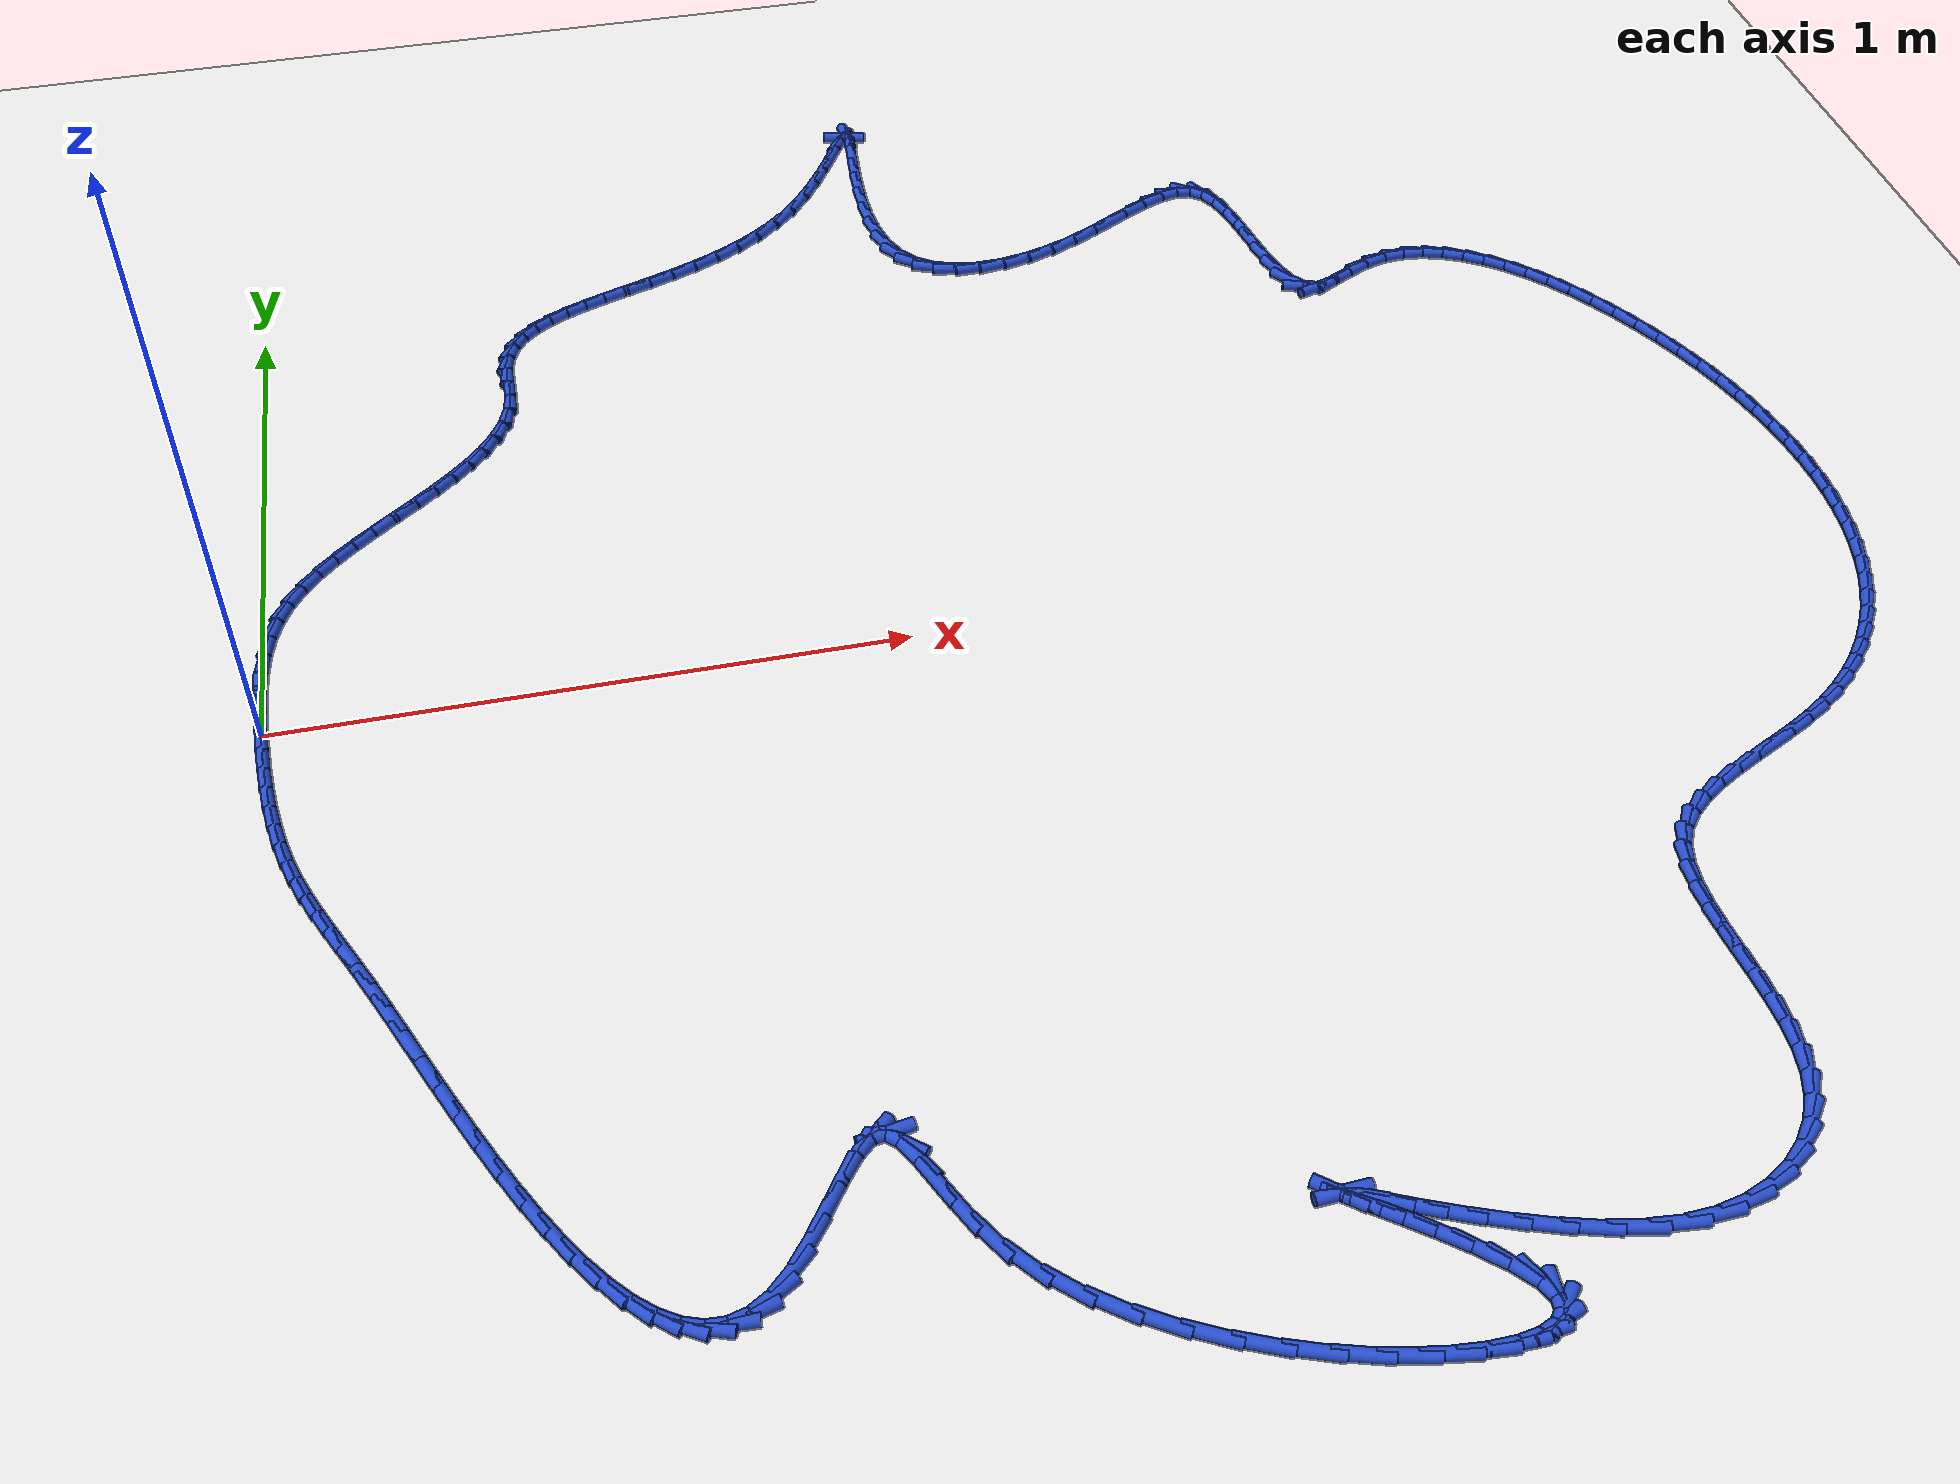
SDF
<sdf version="1.6">
 <world name="default">
  <light name="sun" type="directional">
   <pose>0 0 10 0 -0 0</pose>
   <diffuse>0.8 0.8 0.8 1</diffuse>
   <specular>0.2 0.2 0.2 1</specular>
   <attenuation>
    <range>1000</range>
    <constant>0.9</constant>
    <linear>0.01</linear>
    <quadratic>0.001</quadratic>
   </attenuation>
   <direction>-0.5 0.1 -0.9</direction>
  </light>
  <model name="ground_plane">
   <static>1</static>
   <link name="link">
    <collision name="collision">
     <geometry><plane><normal>0 0 1</normal><size>100 100</size></plane></geometry>
     <surface><friction><ode><mu>100</mu><mu2>50</mu2></ode></friction></surface>
    </collision>
    <visual name="visual">
     <cast_shadows>0</cast_shadows>
     <geometry><plane><normal>0 0 1</normal><size>100 100</size></plane></geometry>
     <material>
      <script><uri>file://media/materials/scripts/gazebo.material</uri><name>Gazebo/WhiteGlow</name></script>
     </material>
    </visual>
   </link>
  </model>
  <gravity>0 0 -9.8</gravity>
  <magnetic_field>6e-06 2.3e-05 -4.2e-05</magnetic_field>
  <atmosphere type="adiabatic"/>
  <physics name="default_physics" default="0" type="ode">
   <max_step_size>0.001</max_step_size>
   <real_time_factor>1</real_time_factor>
   <real_time_update_rate>1000</real_time_update_rate>
  </physics>
  <scene><ambient>0.4 0.4 0.4 1</ambient><background>0.7 0.7 0.7 1</background><shadows>1</shadows></scene>
  <spherical_coordinates>
   <surface_model>EARTH_WGS84</surface_model>
   <latitude_deg>0</latitude_deg>
   <longitude_deg>0</longitude_deg>
   <elevation>0</elevation>
   <heading_deg>0</heading_deg>
  </spherical_coordinates>
  <model name="line">
   <link name="link_0">
    <pose>8.876905287225068e-18 -3.469446951953614e-17 0.01 0 1.57 -1.5388181777335797</pose>
    <collision name="collision">
     <geometry><cylinder><radius>0.01</radius><length>0.08</length></cylinder></geometry>
    </collision>
    <visual name="visual">
     <material>
      <script><name>Gazebo/Blue</name><uri>file://media/materials/scripts/gazebo.material</uri></script>
     </material>
     <geometry><cylinder><radius>0.01</radius><length>0.08</length></cylinder></geometry>
    </visual>
   </link>
   <link name="link_1">
    <pose>-0.0013342330816965733 0.041709051128966085 0.01 0 1.57 -1.5698637900432821</pose>
    <collision name="collision">
     <geometry><cylinder><radius>0.01</radius><length>0.08</length></cylinder></geometry>
    </collision>
    <visual name="visual">
     <material>
      <script><name>Gazebo/Blue</name><uri>file://media/materials/scripts/gazebo.material</uri></script>
     </material>
     <geometry><cylinder><radius>0.01</radius><length>0.08</length></cylinder></geometry>
    </visual>
   </link>
   <link name="link_2">
    <pose>-0.0013729636116146375 0.0832414825575409 0.01 0 1.57 1.5245017664246117</pose>
    <collision name="collision">
     <geometry><cylinder><radius>0.01</radius><length>0.08</length></cylinder></geometry>
    </collision>
    <visual name="visual">
     <material>
      <script><name>Gazebo/Blue</name><uri>file://media/materials/scripts/gazebo.material</uri></script>
     </material>
     <geometry><cylinder><radius>0.01</radius><length>0.08</length></cylinder></geometry>
    </visual>
   </link>
   <link name="link_3">
    <pose>0.0005268423543587468 0.12424950907540658 0.01 0 1.57 1.459601645572316</pose>
    <collision name="collision">
     <geometry><cylinder><radius>0.01</radius><length>0.08</length></cylinder></geometry>
    </collision>
    <visual name="visual">
     <material>
      <script><name>Gazebo/Blue</name><uri>file://media/materials/scripts/gazebo.material</uri></script>
     </material>
     <geometry><cylinder><radius>0.01</radius><length>0.08</length></cylinder></geometry>
    </visual>
   </link>
   <link name="link_4">
    <pose>0.005008218760336513 0.16438534547224498 0.01 0 1.57 1.3753087487566449</pose>
    <collision name="collision">
     <geometry><cylinder><radius>0.01</radius><length>0.08</length></cylinder></geometry>
    </collision>
    <visual name="visual">
     <material>
      <script><name>Gazebo/Blue</name><uri>file://media/materials/scripts/gazebo.material</uri></script>
     </material>
     <geometry><cylinder><radius>0.01</radius><length>0.08</length></cylinder></geometry>
    </visual>
   </link>
   <link name="link_5">
    <pose>0.012714199550431595 0.20330120653773837 0.01 0 1.57 1.2702955046169055</pose>
    <collision name="collision">
     <geometry><cylinder><radius>0.01</radius><length>0.08</length></cylinder></geometry>
    </collision>
    <visual name="visual">
     <material>
      <script><name>Gazebo/Blue</name><uri>file://media/materials/scripts/gazebo.material</uri></script>
     </material>
     <geometry><cylinder><radius>0.01</radius><length>0.08</length></cylinder></geometry>
    </visual>
   </link>
   <link name="link_6">
    <pose>0.024287818668756934 0.24064930706156876 0.01 0 1.57 1.1447108239115833</pose>
    <collision name="collision">
     <geometry><cylinder><radius>0.01</radius><length>0.08</length></cylinder></geometry>
    </collision>
    <visual name="visual">
     <material>
      <script><name>Gazebo/Blue</name><uri>file://media/materials/scripts/gazebo.material</uri></script>
     </material>
     <geometry><cylinder><radius>0.01</radius><length>0.08</length></cylinder></geometry>
    </visual>
   </link>
   <link name="link_7">
    <pose>0.040370669185493216 0.2760825447835628 0.01 0 1.57 1.0122751202134297</pose>
    <collision name="collision">
     <geometry><cylinder><radius>0.01</radius><length>0.08</length></cylinder></geometry>
    </collision>
    <visual name="visual">
     <material>
      <script><name>Gazebo/Blue</name><uri>file://media/materials/scripts/gazebo.material</uri></script>
     </material>
     <geometry><cylinder><radius>0.01</radius><length>0.08</length></cylinder></geometry>
    </visual>
   </link>
   <link name="link_8">
    <pose>0.061214560871536434 0.3094385682081376 0.01 0 1.57 0.9018552316565003</pose>
    <collision name="collision">
     <geometry><cylinder><radius>0.01</radius><length>0.08</length></cylinder></geometry>
    </collision>
    <visual name="visual">
     <material>
      <script><name>Gazebo/Blue</name><uri>file://media/materials/scripts/gazebo.material</uri></script>
     </material>
     <geometry><cylinder><radius>0.01</radius><length>0.08</length></cylinder></geometry>
    </visual>
   </link>
   <link name="link_9">
    <pose>0.08615605962513373 0.34098883612755043 0.01 0 1.57 0.8168288669703682</pose>
    <collision name="collision">
     <geometry><cylinder><radius>0.01</radius><length>0.08</length></cylinder></geometry>
    </collision>
    <visual name="visual">
     <material>
      <script><name>Gazebo/Blue</name><uri>file://media/materials/scripts/gazebo.material</uri></script>
     </material>
     <geometry><cylinder><radius>0.01</radius><length>0.08</length></cylinder></geometry>
    </visual>
   </link>
   <link name="link_10">
    <pose>0.11440050513459779 0.371067006362761 0.01 0 1.57 0.755035127044355</pose>
    <collision name="collision">
     <geometry><cylinder><radius>0.01</radius><length>0.08</length></cylinder></geometry>
    </collision>
    <visual name="visual">
     <material>
      <script><name>Gazebo/Blue</name><uri>file://media/materials/scripts/gazebo.material</uri></script>
     </material>
     <geometry><cylinder><radius>0.01</radius><length>0.08</length></cylinder></geometry>
    </visual>
   </link>
   <link name="link_11">
    <pose>0.1451532370882413 0.4000067367347282 0.01 0 1.57 0.7140456324286072</pose>
    <collision name="collision">
     <geometry><cylinder><radius>0.01</radius><length>0.08</length></cylinder></geometry>
    </collision>
    <visual name="visual">
     <material>
      <script><name>Gazebo/Blue</name><uri>file://media/materials/scripts/gazebo.material</uri></script>
     </material>
     <geometry><cylinder><radius>0.01</radius><length>0.08</length></cylinder></geometry>
    </visual>
   </link>
   <link name="link_12">
    <pose>0.17761959517437706 0.42814168506441186 0.01 0 1.57 0.6919515488639092</pose>
    <collision name="collision">
     <geometry><cylinder><radius>0.01</radius><length>0.08</length></cylinder></geometry>
    </collision>
    <visual name="visual">
     <material>
      <script><name>Gazebo/Blue</name><uri>file://media/materials/scripts/gazebo.material</uri></script>
     </material>
     <geometry><cylinder><radius>0.01</radius><length>0.08</length></cylinder></geometry>
    </visual>
   </link>
   <link name="link_13">
    <pose>0.21100491908131758 0.45580550917277074 0.01 0 1.57 0.6876817813719777</pose>
    <collision name="collision">
     <geometry><cylinder><radius>0.01</radius><length>0.08</length></cylinder></geometry>
    </collision>
    <visual name="visual">
     <material>
      <script><name>Gazebo/Blue</name><uri>file://media/materials/scripts/gazebo.material</uri></script>
     </material>
     <geometry><cylinder><radius>0.01</radius><length>0.08</length></cylinder></geometry>
    </visual>
   </link>
   <link name="link_14">
    <pose>0.24451454849737567 0.4833318668807645 0.01 0 1.57 0.7011106968436897</pose>
    <collision name="collision">
     <geometry><cylinder><radius>0.01</radius><length>0.08</length></cylinder></geometry>
    </collision>
    <visual name="visual">
     <material>
      <script><name>Gazebo/Blue</name><uri>file://media/materials/scripts/gazebo.material</uri></script>
     </material>
     <geometry><cylinder><radius>0.01</radius><length>0.08</length></cylinder></geometry>
    </visual>
   </link>
   <link name="link_15">
    <pose>0.27735382311086404 0.5110544160093524 0.01 0 1.57 0.7330891234743963</pose>
    <collision name="collision">
     <geometry><cylinder><radius>0.01</radius><length>0.08</length></cylinder></geometry>
    </collision>
    <visual name="visual">
     <material>
      <script><name>Gazebo/Blue</name><uri>file://media/materials/scripts/gazebo.material</uri></script>
     </material>
     <geometry><cylinder><radius>0.01</radius><length>0.08</length></cylinder></geometry>
    </visual>
   </link>
   <link name="link_16">
    <pose>0.3087280826100953 0.5393068143794939 0.01 0 1.57 0.7854208552789375</pose>
    <collision name="collision">
     <geometry><cylinder><radius>0.01</radius><length>0.08</length></cylinder></geometry>
    </collision>
    <visual name="visual">
     <material>
      <script><name>Gazebo/Blue</name><uri>file://media/materials/scripts/gazebo.material</uri></script>
     </material>
     <geometry><cylinder><radius>0.01</radius><length>0.08</length></cylinder></geometry>
    </visual>
   </link>
   <link name="link_17">
    <pose>0.3378426666833825 0.5684227198121482 0.01 0 1.57 0.8606958675477416</pose>
    <collision name="collision">
     <geometry><cylinder><radius>0.01</radius><length>0.08</length></cylinder></geometry>
    </collision>
    <visual name="visual">
     <material>
      <script><name>Gazebo/Blue</name><uri>file://media/materials/scripts/gazebo.material</uri></script>
     </material>
     <geometry><cylinder><radius>0.01</radius><length>0.08</length></cylinder></geometry>
    </visual>
   </link>
   <link name="link_18">
    <pose>0.36390291501903776 0.5987357901282744 0.01 0 1.57 0.961747293952969</pose>
    <collision name="collision">
     <geometry><cylinder><radius>0.01</radius><length>0.08</length></cylinder></geometry>
    </collision>
    <visual name="visual">
     <material>
      <script><name>Gazebo/Blue</name><uri>file://media/materials/scripts/gazebo.material</uri></script>
     </material>
     <geometry><cylinder><radius>0.01</radius><length>0.08</length></cylinder></geometry>
    </visual>
   </link>
   <link name="link_19">
    <pose>0.3861141673053741 0.6305796831488322 0.01 0 1.57 1.090361104754436</pose>
    <collision name="collision">
     <geometry><cylinder><radius>0.01</radius><length>0.08</length></cylinder></geometry>
    </collision>
    <visual name="visual">
     <material>
      <script><name>Gazebo/Blue</name><uri>file://media/materials/scripts/gazebo.material</uri></script>
     </material>
     <geometry><cylinder><radius>0.01</radius><length>0.08</length></cylinder></geometry>
    </visual>
   </link>
   <link name="link_20">
    <pose>0.40368176323070426 0.6642880566947806 0.01 0 1.57 1.2450296853127885</pose>
    <collision name="collision">
     <geometry><cylinder><radius>0.01</radius><length>0.08</length></cylinder></geometry>
    </collision>
    <visual name="visual">
     <material>
      <script><name>Gazebo/Blue</name><uri>file://media/materials/scripts/gazebo.material</uri></script>
     </material>
     <geometry><cylinder><radius>0.01</radius><length>0.08</length></cylinder></geometry>
    </visual>
   </link>
   <link name="link_21">
    <pose>0.4158110424833407 0.7001945685870792 0.01 0 1.57 1.4185862764887112</pose>
    <collision name="collision">
     <geometry><cylinder><radius>0.01</radius><length>0.08</length></cylinder></geometry>
    </collision>
    <visual name="visual">
     <material>
      <script><name>Gazebo/Blue</name><uri>file://media/materials/scripts/gazebo.material</uri></script>
     </material>
     <geometry><cylinder><radius>0.01</radius><length>0.08</length></cylinder></geometry>
    </visual>
   </link>
   <link name="link_22">
    <pose>0.4217073447515963 0.738632876646687 0.01 0 1.57 1.5682580806572348</pose>
    <collision name="collision">
     <geometry><cylinder><radius>0.01</radius><length>0.08</length></cylinder></geometry>
    </collision>
    <visual name="visual">
     <material>
      <script><name>Gazebo/Blue</name><uri>file://media/materials/scripts/gazebo.material</uri></script>
     </material>
     <geometry><cylinder><radius>0.01</radius><length>0.08</length></cylinder></geometry>
    </visual>
   </link>
   <link name="link_23">
    <pose>0.4218103912208103 0.7792302979865614 0.01 0 1.57 -1.5638474936969518</pose>
    <collision name="collision">
     <geometry><cylinder><radius>0.01</radius><length>0.08</length></cylinder></geometry>
    </collision>
    <visual name="visual">
     <material>
      <script><name>Gazebo/Blue</name><uri>file://media/materials/scripts/gazebo.material</uri></script>
     </material>
     <geometry><cylinder><radius>0.01</radius><length>0.08</length></cylinder></geometry>
    </visual>
   </link>
   <link name="link_24">
    <pose>0.42153565345257815 0.8187669140376008 0.01 0 1.57 1.4255696961304651</pose>
    <collision name="collision">
     <geometry><cylinder><radius>0.01</radius><length>0.08</length></cylinder></geometry>
    </collision>
    <visual name="visual">
     <material>
      <script><name>Gazebo/Blue</name><uri>file://media/materials/scripts/gazebo.material</uri></script>
     </material>
     <geometry><cylinder><radius>0.01</radius><length>0.08</length></cylinder></geometry>
    </visual>
   </link>
   <link name="link_25">
    <pose>0.42666865754295463 0.8538628663581784 0.01 0 1.57 1.2064040408737093</pose>
    <collision name="collision">
     <geometry><cylinder><radius>0.01</radius><length>0.08</length></cylinder></geometry>
    </collision>
    <visual name="visual">
     <material>
      <script><name>Gazebo/Blue</name><uri>file://media/materials/scripts/gazebo.material</uri></script>
     </material>
     <geometry><cylinder><radius>0.01</radius><length>0.08</length></cylinder></geometry>
    </visual>
   </link>
   <link name="link_26">
    <pose>0.43822096429051716 0.8841500353936307 0.01 0 1.57 0.9837804922667585</pose>
    <collision name="collision">
     <geometry><cylinder><radius>0.01</radius><length>0.08</length></cylinder></geometry>
    </collision>
    <visual name="visual">
     <material>
      <script><name>Gazebo/Blue</name><uri>file://media/materials/scripts/gazebo.material</uri></script>
     </material>
     <geometry><cylinder><radius>0.01</radius><length>0.08</length></cylinder></geometry>
    </visual>
   </link>
   <link name="link_27">
    <pose>0.45559901200173475 0.9102729209789628 0.01 0 1.57 0.7852838173489628</pose>
    <collision name="collision">
     <geometry><cylinder><radius>0.01</radius><length>0.08</length></cylinder></geometry>
    </collision>
    <visual name="visual">
     <material>
      <script><name>Gazebo/Blue</name><uri>file://media/materials/scripts/gazebo.material</uri></script>
     </material>
     <geometry><cylinder><radius>0.01</radius><length>0.08</length></cylinder></geometry>
    </visual>
   </link>
   <link name="link_28">
    <pose>0.4782080401754692 0.9328767792377706 0.01 0 1.57 0.626761427421215</pose>
    <collision name="collision">
     <geometry><cylinder><radius>0.01</radius><length>0.08</length></cylinder></geometry>
    </collision>
    <visual name="visual">
     <material>
      <script><name>Gazebo/Blue</name><uri>file://media/materials/scripts/gazebo.material</uri></script>
     </material>
     <geometry><cylinder><radius>0.01</radius><length>0.08</length></cylinder></geometry>
    </visual>
   </link>
   <link name="link_29">
    <pose>0.5054532883105821 0.9526068662936499 0.01 0 1.57 0.5100262778672222</pose>
    <collision name="collision">
     <geometry><cylinder><radius>0.01</radius><length>0.08</length></cylinder></geometry>
    </collision>
    <visual name="visual">
     <material>
      <script><name>Gazebo/Blue</name><uri>file://media/materials/scripts/gazebo.material</uri></script>
     </material>
     <geometry><cylinder><radius>0.01</radius><length>0.08</length></cylinder></geometry>
    </visual>
   </link>
   <link name="link_30">
    <pose>0.5367399959059351 0.9701084382701959 0.01 0 1.57 0.4297345607355648</pose>
    <collision name="collision">
     <geometry><cylinder><radius>0.01</radius><length>0.08</length></cylinder></geometry>
    </collision>
    <visual name="visual">
     <material>
      <script><name>Gazebo/Blue</name><uri>file://media/materials/scripts/gazebo.material</uri></script>
     </material>
     <geometry><cylinder><radius>0.01</radius><length>0.08</length></cylinder></geometry>
    </visual>
   </link>
   <link name="link_31">
    <pose>0.5714734024603907 0.9860267512910053 0.01 0 1.57 0.3792711564800059</pose>
    <collision name="collision">
     <geometry><cylinder><radius>0.01</radius><length>0.08</length></cylinder></geometry>
    </collision>
    <visual name="visual">
     <material>
      <script><name>Gazebo/Blue</name><uri>file://media/materials/scripts/gazebo.material</uri></script>
     </material>
     <geometry><cylinder><radius>0.01</radius><length>0.08</length></cylinder></geometry>
    </visual>
   </link>
   <link name="link_32">
    <pose>0.60905874747281 1.0010070614796733 0.01 0 1.57 0.35318350402038323</pose>
    <collision name="collision">
     <geometry><cylinder><radius>0.01</radius><length>0.08</length></cylinder></geometry>
    </collision>
    <visual name="visual">
     <material>
      <script><name>Gazebo/Blue</name><uri>file://media/materials/scripts/gazebo.material</uri></script>
     </material>
     <geometry><cylinder><radius>0.01</radius><length>0.08</length></cylinder></geometry>
    </visual>
   </link>
   <link name="link_33">
    <pose>0.648901270442055 1.0156946249597967 0.01 0 1.57 0.3476505406244318</pose>
    <collision name="collision">
     <geometry><cylinder><radius>0.01</radius><length>0.08</length></cylinder></geometry>
    </collision>
    <visual name="visual">
     <material>
      <script><name>Gazebo/Blue</name><uri>file://media/materials/scripts/gazebo.material</uri></script>
     </material>
     <geometry><cylinder><radius>0.01</radius><length>0.08</length></cylinder></geometry>
    </visual>
   </link>
   <link name="link_34">
    <pose>0.6904062108669875 1.0307346978549699 0.01 0 1.57 0.36027549012289645</pose>
    <collision name="collision">
     <geometry><cylinder><radius>0.01</radius><length>0.08</length></cylinder></geometry>
    </collision>
    <visual name="visual">
     <material>
      <script><name>Gazebo/Blue</name><uri>file://media/materials/scripts/gazebo.material</uri></script>
     </material>
     <geometry><cylinder><radius>0.01</radius><length>0.08</length></cylinder></geometry>
    </visual>
   </link>
   <link name="link_35">
    <pose>0.7329788082464694 1.0467725362887899 0.01 0 1.57 0.3897376097522639</pose>
    <collision name="collision">
     <geometry><cylinder><radius>0.01</radius><length>0.08</length></cylinder></geometry>
    </collision>
    <visual name="visual">
     <material>
      <script><name>Gazebo/Blue</name><uri>file://media/materials/scripts/gazebo.material</uri></script>
     </material>
     <geometry><cylinder><radius>0.01</radius><length>0.08</length></cylinder></geometry>
    </visual>
   </link>
   <link name="link_36">
    <pose>0.7760243020793626 1.064453396384852 0.01 0 1.57 0.4354425065101532</pose>
    <collision name="collision">
     <geometry><cylinder><radius>0.01</radius><length>0.08</length></cylinder></geometry>
    </collision>
    <visual name="visual">
     <material>
      <script><name>Gazebo/Blue</name><uri>file://media/materials/scripts/gazebo.material</uri></script>
     </material>
     <geometry><cylinder><radius>0.01</radius><length>0.08</length></cylinder></geometry>
    </visual>
   </link>
   <link name="link_37">
    <pose>0.8189479318645285 1.0844225342667522 0.01 0 1.57 0.49716514496578956</pose>
    <collision name="collision">
     <geometry><cylinder><radius>0.01</radius><length>0.08</length></cylinder></geometry>
    </collision>
    <visual name="visual">
     <material>
      <script><name>Gazebo/Blue</name><uri>file://media/materials/scripts/gazebo.material</uri></script>
     </material>
     <geometry><cylinder><radius>0.01</radius><length>0.08</length></cylinder></geometry>
    </visual>
   </link>
   <link name="link_38">
    <pose>0.8611549371008289 1.1073252060580863 0.01 0 1.57 0.5746424091434937</pose>
    <collision name="collision">
     <geometry><cylinder><radius>0.01</radius><length>0.08</length></cylinder></geometry>
    </collision>
    <visual name="visual">
     <material>
      <script><name>Gazebo/Blue</name><uri>file://media/materials/scripts/gazebo.material</uri></script>
     </material>
     <geometry><cylinder><radius>0.01</radius><length>0.08</length></cylinder></geometry>
    </visual>
   </link>
   <link name="link_39">
    <pose>0.902050557287126 1.1338066678824499 0.01 0 1.57 0.6670929081125562</pose>
    <collision name="collision">
     <geometry><cylinder><radius>0.01</radius><length>0.08</length></cylinder></geometry>
    </collision>
    <visual name="visual">
     <material>
      <script><name>Gazebo/Blue</name><uri>file://media/materials/scripts/gazebo.material</uri></script>
     </material>
     <geometry><cylinder><radius>0.01</radius><length>0.08</length></cylinder></geometry>
    </visual>
   </link>
   <link name="link_40">
    <pose>0.9410400319222816 1.1645121758634391 0.01 0 1.57 0.7727189167463834</pose>
    <collision name="collision">
     <geometry><cylinder><radius>0.01</radius><length>0.08</length></cylinder></geometry>
    </collision>
    <visual name="visual">
     <material>
      <script><name>Gazebo/Blue</name><uri>file://media/materials/scripts/gazebo.material</uri></script>
     </material>
     <geometry><cylinder><radius>0.01</radius><length>0.08</length></cylinder></geometry>
    </visual>
   </link>
   <link name="link_41">
    <pose>0.9775286005051571 1.2000869861246501 0.01 0 1.57 0.8853441486444519</pose>
    <collision name="collision">
     <geometry><cylinder><radius>0.01</radius><length>0.08</length></cylinder></geometry>
    </collision>
    <visual name="visual">
     <material>
      <script><name>Gazebo/Blue</name><uri>file://media/materials/scripts/gazebo.material</uri></script>
     </material>
     <geometry><cylinder><radius>0.01</radius><length>0.08</length></cylinder></geometry>
    </visual>
   </link>
   <link name="link_42">
    <pose>1.0109446838249232 1.2409519848049575 0.01 0 1.57 0.9755425239559367</pose>
    <collision name="collision">
     <geometry><cylinder><radius>0.01</radius><length>0.08</length></cylinder></geometry>
    </collision>
    <visual name="visual">
     <material>
      <script><name>Gazebo/Blue</name><uri>file://media/materials/scripts/gazebo.material</uri></script>
     </material>
     <geometry><cylinder><radius>0.01</radius><length>0.08</length></cylinder></geometry>
    </visual>
   </link>
   <link name="link_43">
    <pose>1.040950856286816 1.2852617026091506 0.01 0 1.57 1.0363660029310606</pose>
    <collision name="collision">
     <geometry><cylinder><radius>0.01</radius><length>0.08</length></cylinder></geometry>
    </collision>
    <visual name="visual">
     <material>
      <script><name>Gazebo/Blue</name><uri>file://media/materials/scripts/gazebo.material</uri></script>
     </material>
     <geometry><cylinder><radius>0.01</radius><length>0.08</length></cylinder></geometry>
    </visual>
   </link>
   <link name="link_44">
    <pose>1.0673455170793091 1.3298560322674264 0.01 0 1.57 1.0744800186145083</pose>
    <collision name="collision">
     <geometry><cylinder><radius>0.01</radius><length>0.08</length></cylinder></geometry>
    </collision>
    <visual name="visual">
     <material>
      <script><name>Gazebo/Blue</name><uri>file://media/materials/scripts/gazebo.material</uri></script>
     </material>
     <geometry><cylinder><radius>0.01</radius><length>0.08</length></cylinder></geometry>
    </visual>
   </link>
   <link name="link_45">
    <pose>1.0899287333122232 1.3715587228233062 0.01 0 1.57 1.0903554069538983</pose>
    <collision name="collision">
     <geometry><cylinder><radius>0.01</radius><length>0.08</length></cylinder></geometry>
    </collision>
    <visual name="visual">
     <material>
      <script><name>Gazebo/Blue</name><uri>file://media/materials/scripts/gazebo.material</uri></script>
     </material>
     <geometry><cylinder><radius>0.01</radius><length>0.08</length></cylinder></geometry>
    </visual>
   </link>
   <link name="link_46">
    <pose>1.1085005720953804 1.4071935233203112 0.01 0 1.57 1.0724540769323248</pose>
    <collision name="collision">
     <geometry><cylinder><radius>0.01</radius><length>0.08</length></cylinder></geometry>
    </collision>
    <visual name="visual">
     <material>
      <script><name>Gazebo/Blue</name><uri>file://media/materials/scripts/gazebo.material</uri></script>
     </material>
     <geometry><cylinder><radius>0.01</radius><length>0.08</length></cylinder></geometry>
    </visual>
   </link>
   <link name="link_47">
    <pose>1.1228611005386016 1.4335841828019622 0.01 0 1.57 0.9519453991845559</pose>
    <collision name="collision">
     <geometry><cylinder><radius>0.01</radius><length>0.08</length></cylinder></geometry>
    </collision>
    <visual name="visual">
     <material>
      <script><name>Gazebo/Blue</name><uri>file://media/materials/scripts/gazebo.material</uri></script>
     </material>
     <geometry><cylinder><radius>0.01</radius><length>0.08</length></cylinder></geometry>
    </visual>
   </link>
   <link name="link_48">
    <pose>1.1328103857517076 1.4475544503117803 0.01 0 1.57 -0.2323092207733221</pose>
    <collision name="collision">
     <geometry><cylinder><radius>0.01</radius><length>0.08</length></cylinder></geometry>
    </collision>
    <visual name="visual">
     <material>
      <script><name>Gazebo/Blue</name><uri>file://media/materials/scripts/gazebo.material</uri></script>
     </material>
     <geometry><cylinder><radius>0.01</radius><length>0.08</length></cylinder></geometry>
    </visual>
   </link>
   <link name="link_49">
    <pose>1.1382302597067393 1.44627221380061 0.01 0 1.57 -1.4732201761016894</pose>
    <collision name="collision">
     <geometry><cylinder><radius>0.01</radius><length>0.08</length></cylinder></geometry>
    </collision>
    <visual name="visual">
     <material>
      <script><name>Gazebo/Blue</name><uri>file://media/materials/scripts/gazebo.material</uri></script>
     </material>
     <geometry><cylinder><radius>0.01</radius><length>0.08</length></cylinder></geometry>
    </visual>
   </link>
   <link name="link_50">
    <pose>1.1397982147856793 1.4302542044344162 0.01 0 1.57 1.5299649811855243</pose>
    <collision name="collision">
     <geometry><cylinder><radius>0.01</radius><length>0.08</length></cylinder></geometry>
    </collision>
    <visual name="visual">
     <material>
      <script><name>Gazebo/Blue</name><uri>file://media/materials/scripts/gazebo.material</uri></script>
     </material>
     <geometry><cylinder><radius>0.01</radius><length>0.08</length></cylinder></geometry>
    </visual>
   </link>
   <link name="link_51">
    <pose>1.1386399836471184 1.4019037451842946 0.01 0 1.57 1.4989449881171628</pose>
    <collision name="collision">
     <geometry><cylinder><radius>0.01</radius><length>0.08</length></cylinder></geometry>
    </collision>
    <visual name="visual">
     <material>
      <script><name>Gazebo/Blue</name><uri>file://media/materials/scripts/gazebo.material</uri></script>
     </material>
     <geometry><cylinder><radius>0.01</radius><length>0.08</length></cylinder></geometry>
    </visual>
   </link>
   <link name="link_52">
    <pose>1.1358863232189613 1.3636453055934095 0.01 0 1.57 1.5005536306053475</pose>
    <collision name="collision">
     <geometry><cylinder><radius>0.01</radius><length>0.08</length></cylinder></geometry>
    </collision>
    <visual name="visual">
     <material>
      <script><name>Gazebo/Blue</name><uri>file://media/materials/scripts/gazebo.material</uri></script>
     </material>
     <geometry><cylinder><radius>0.01</radius><length>0.08</length></cylinder></geometry>
    </visual>
   </link>
   <link name="link_53">
    <pose>1.132667990429113 1.3179033552049266 0.01 0 1.57 1.5205984067136467</pose>
    <collision name="collision">
     <geometry><cylinder><radius>0.01</radius><length>0.08</length></cylinder></geometry>
    </collision>
    <visual name="visual">
     <material>
      <script><name>Gazebo/Blue</name><uri>file://media/materials/scripts/gazebo.material</uri></script>
     </material>
     <geometry><cylinder><radius>0.01</radius><length>0.08</length></cylinder></geometry>
    </visual>
   </link>
   <link name="link_54">
    <pose>1.1301157422054775 1.2671023635620111 0.01 0 1.57 1.5566604898010765</pose>
    <collision name="collision">
     <geometry><cylinder><radius>0.01</radius><length>0.08</length></cylinder></geometry>
    </collision>
    <visual name="visual">
     <material>
      <script><name>Gazebo/Blue</name><uri>file://media/materials/scripts/gazebo.material</uri></script>
     </material>
     <geometry><cylinder><radius>0.01</radius><length>0.08</length></cylinder></geometry>
    </visual>
   </link>
   <link name="link_55">
    <pose>1.12936033547596 1.213666800207829 0.01 0 1.57 -1.5303269674825457</pose>
    <collision name="collision">
     <geometry><cylinder><radius>0.01</radius><length>0.08</length></cylinder></geometry>
    </collision>
    <visual name="visual">
     <material>
      <script><name>Gazebo/Blue</name><uri>file://media/materials/scripts/gazebo.material</uri></script>
     </material>
     <geometry><cylinder><radius>0.01</radius><length>0.08</length></cylinder></geometry>
    </visual>
   </link>
   <link name="link_56">
    <pose>1.1315325271684649 1.1600211346855445 0.01 0 1.57 -1.4502406777522936</pose>
    <collision name="collision">
     <geometry><cylinder><radius>0.01</radius><length>0.08</length></cylinder></geometry>
    </collision>
    <visual name="visual">
     <material>
      <script><name>Gazebo/Blue</name><uri>file://media/materials/scripts/gazebo.material</uri></script>
     </material>
     <geometry><cylinder><radius>0.01</radius><length>0.08</length></cylinder></geometry>
    </visual>
   </link>
   <link name="link_57">
    <pose>1.137763074210897 1.1085898365383233 0.01 0 1.57 -1.3314262796579297</pose>
    <collision name="collision">
     <geometry><cylinder><radius>0.01</radius><length>0.08</length></cylinder></geometry>
    </collision>
    <visual name="visual">
     <material>
      <script><name>Gazebo/Blue</name><uri>file://media/materials/scripts/gazebo.material</uri></script>
     </material>
     <geometry><cylinder><radius>0.01</radius><length>0.08</length></cylinder></geometry>
    </visual>
   </link>
   <link name="link_58">
    <pose>1.1491827335311606 1.0617973753093313 0.01 0 1.57 -1.15084781916414</pose>
    <collision name="collision">
     <geometry><cylinder><radius>0.01</radius><length>0.08</length></cylinder></geometry>
    </collision>
    <visual name="visual">
     <material>
      <script><name>Gazebo/Blue</name><uri>file://media/materials/scripts/gazebo.material</uri></script>
     </material>
     <geometry><cylinder><radius>0.01</radius><length>0.08</length></cylinder></geometry>
    </visual>
   </link>
   <link name="link_59">
    <pose>1.1669222420590948 1.0220681927908972 0.01 0 1.57 -0.893102407904086</pose>
    <collision name="collision">
     <geometry><cylinder><radius>0.01</radius><length>0.08</length></cylinder></geometry>
    </collision>
    <visual name="visual">
     <material>
      <script><name>Gazebo/Blue</name><uri>file://media/materials/scripts/gazebo.material</uri></script>
     </material>
     <geometry><cylinder><radius>0.01</radius><length>0.08</length></cylinder></geometry>
    </visual>
   </link>
   <link name="link_60">
    <pose>1.1917107442021784 0.991269450482976 0.01 0 1.57 -0.6149293826047683</pose>
    <collision name="collision">
     <geometry><cylinder><radius>0.01</radius><length>0.08</length></cylinder></geometry>
    </collision>
    <visual name="visual">
     <material>
      <script><name>Gazebo/Blue</name><uri>file://media/materials/scripts/gazebo.material</uri></script>
     </material>
     <geometry><cylinder><radius>0.01</radius><length>0.08</length></cylinder></geometry>
    </visual>
   </link>
   <link name="link_61">
    <pose>1.2228446530753259 0.9692801431016254 0.01 0 1.57 -0.36052347984355465</pose>
    <collision name="collision">
     <geometry><cylinder><radius>0.01</radius><length>0.08</length></cylinder></geometry>
    </collision>
    <visual name="visual">
     <material>
      <script><name>Gazebo/Blue</name><uri>file://media/materials/scripts/gazebo.material</uri></script>
     </material>
     <geometry><cylinder><radius>0.01</radius><length>0.08</length></cylinder></geometry>
    </visual>
   </link>
   <link name="link_62">
    <pose>1.2593010062048173 0.9555360755336589 0.01 0 1.57 -0.1476814513638622</pose>
    <collision name="collision">
     <geometry><cylinder><radius>0.01</radius><length>0.08</length></cylinder></geometry>
    </collision>
    <visual name="visual">
     <material>
      <script><name>Gazebo/Blue</name><uri>file://media/materials/scripts/gazebo.material</uri></script>
     </material>
     <geometry><cylinder><radius>0.01</radius><length>0.08</length></cylinder></geometry>
    </visual>
   </link>
   <link name="link_63">
    <pose>1.3000568411169346 0.9494730526658889 0.01 0 1.57 0.023928440807852468</pose>
    <collision name="collision">
     <geometry><cylinder><radius>0.01</radius><length>0.08</length></cylinder></geometry>
    </collision>
    <visual name="visual">
     <material>
      <script><name>Gazebo/Blue</name><uri>file://media/materials/scripts/gazebo.material</uri></script>
     </material>
     <geometry><cylinder><radius>0.01</radius><length>0.08</length></cylinder></geometry>
    </visual>
   </link>
   <link name="link_64">
    <pose>1.3440891953379583 0.9505268793851279 0.01 0 1.57 0.16288098369406465</pose>
    <collision name="collision">
     <geometry><cylinder><radius>0.01</radius><length>0.08</length></cylinder></geometry>
    </collision>
    <visual name="visual">
     <material>
      <script><name>Gazebo/Blue</name><uri>file://media/materials/scripts/gazebo.material</uri></script>
     </material>
     <geometry><cylinder><radius>0.01</radius><length>0.08</length></cylinder></geometry>
    </visual>
   </link>
   <link name="link_65">
    <pose>1.390375106394169 0.9581333605781887 0.01 0 1.57 0.2786653373070162</pose>
    <collision name="collision">
     <geometry><cylinder><radius>0.01</radius><length>0.08</length></cylinder></geometry>
    </collision>
    <visual name="visual">
     <material>
      <script><name>Gazebo/Blue</name><uri>file://media/materials/scripts/gazebo.material</uri></script>
     </material>
     <geometry><cylinder><radius>0.01</radius><length>0.08</length></cylinder></geometry>
    </visual>
   </link>
   <link name="link_66">
    <pose>1.437891611811849 0.9717283011318847 0.01 0 1.57 0.37923309288285934</pose>
    <collision name="collision">
     <geometry><cylinder><radius>0.01</radius><length>0.08</length></cylinder></geometry>
    </collision>
    <visual name="visual">
     <material>
      <script><name>Gazebo/Blue</name><uri>file://media/materials/scripts/gazebo.material</uri></script>
     </material>
     <geometry><cylinder><radius>0.01</radius><length>0.08</length></cylinder></geometry>
    </visual>
   </link>
   <link name="link_67">
    <pose>1.4856157495907836 0.9907475030734277 0.01 0 1.57 0.46410003968894264</pose>
    <collision name="collision">
     <geometry><cylinder><radius>0.01</radius><length>0.08</length></cylinder></geometry>
    </collision>
    <visual name="visual">
     <material>
      <script><name>Gazebo/Blue</name><uri>file://media/materials/scripts/gazebo.material</uri></script>
     </material>
     <geometry><cylinder><radius>0.01</radius><length>0.08</length></cylinder></geometry>
    </visual>
   </link>
   <link name="link_68">
    <pose>1.5325854659822682 1.0142589304577267 0.01 0 1.57 0.514105577774927</pose>
    <collision name="collision">
     <geometry><cylinder><radius>0.01</radius><length>0.08</length></cylinder></geometry>
    </collision>
    <visual name="visual">
     <material>
      <script><name>Gazebo/Blue</name><uri>file://media/materials/scripts/gazebo.material</uri></script>
     </material>
     <geometry><cylinder><radius>0.01</radius><length>0.08</length></cylinder></geometry>
    </visual>
   </link>
   <link name="link_69">
    <pose>1.5780680142461312 1.0399457132167835 0.01 0 1.57 0.5272373039017425</pose>
    <collision name="collision">
     <geometry><cylinder><radius>0.01</radius><length>0.08</length></cylinder></geometry>
    </collision>
    <visual name="visual">
     <material>
      <script><name>Gazebo/Blue</name><uri>file://media/materials/scripts/gazebo.material</uri></script>
     </material>
     <geometry><cylinder><radius>0.01</radius><length>0.08</length></cylinder></geometry>
    </visual>
   </link>
   <link name="link_70">
    <pose>1.6213846011531745 1.0651651444775267 0.01 0 1.57 0.49999067794593915</pose>
    <collision name="collision">
     <geometry><cylinder><radius>0.01</radius><length>0.08</length></cylinder></geometry>
    </collision>
    <visual name="visual">
     <material>
      <script><name>Gazebo/Blue</name><uri>file://media/materials/scripts/gazebo.material</uri></script>
     </material>
     <geometry><cylinder><radius>0.01</radius><length>0.08</length></cylinder></geometry>
    </visual>
   </link>
   <link name="link_71">
    <pose>1.6618564334741963 1.0872745173668839 0.01 0 1.57 0.41675768130560054</pose>
    <collision name="collision">
     <geometry><cylinder><radius>0.01</radius><length>0.08</length></cylinder></geometry>
    </collision>
    <visual name="visual">
     <material>
      <script><name>Gazebo/Blue</name><uri>file://media/materials/scripts/gazebo.material</uri></script>
     </material>
     <geometry><cylinder><radius>0.01</radius><length>0.08</length></cylinder></geometry>
    </visual>
   </link>
   <link name="link_72">
    <pose>1.6988047179799985 1.103631125011783 0.01 0 1.57 0.238491281110206</pose>
    <collision name="collision">
     <geometry><cylinder><radius>0.01</radius><length>0.08</length></cylinder></geometry>
    </collision>
    <visual name="visual">
     <material>
      <script><name>Gazebo/Blue</name><uri>file://media/materials/scripts/gazebo.material</uri></script>
     </material>
     <geometry><cylinder><radius>0.01</radius><length>0.08</length></cylinder></geometry>
    </visual>
   </link>
   <link name="link_73">
    <pose>1.7315506614413805 1.1115922605391524 0.01 0 1.57 -0.10998197587185295</pose>
    <collision name="collision">
     <geometry><cylinder><radius>0.01</radius><length>0.08</length></cylinder></geometry>
    </collision>
    <visual name="visual">
     <material>
      <script><name>Gazebo/Blue</name><uri>file://media/materials/scripts/gazebo.material</uri></script>
     </material>
     <geometry><cylinder><radius>0.01</radius><length>0.08</length></cylinder></geometry>
    </visual>
   </link>
   <link name="link_74">
    <pose>1.7594154706291425 1.1085152170759192 0.01 0 1.57 -0.6438925608933275</pose>
    <collision name="collision">
     <geometry><cylinder><radius>0.01</radius><length>0.08</length></cylinder></geometry>
    </collision>
    <visual name="visual">
     <material>
      <script><name>Gazebo/Blue</name><uri>file://media/materials/scripts/gazebo.material</uri></script>
     </material>
     <geometry><cylinder><radius>0.01</radius><length>0.08</length></cylinder></geometry>
    </visual>
   </link>
   <link name="link_75">
    <pose>1.7817245136449698 1.0917697856158797 0.01 0 1.57 -1.0768141675435978</pose>
    <collision name="collision">
     <geometry><cylinder><radius>0.01</radius><length>0.08</length></cylinder></geometry>
    </collision>
    <visual name="visual">
     <material>
      <script><name>Gazebo/Blue</name><uri>file://media/materials/scripts/gazebo.material</uri></script>
     </material>
     <geometry><cylinder><radius>0.01</radius><length>0.08</length></cylinder></geometry>
    </visual>
   </link>
   <link name="link_76">
    <pose>1.7984587988746232 1.060694863962529 0.01 0 1.57 -1.2811954678076198</pose>
    <collision name="collision">
     <geometry><cylinder><radius>0.01</radius><length>0.08</length></cylinder></geometry>
    </collision>
    <visual name="visual">
     <material>
      <script><name>Gazebo/Blue</name><uri>file://media/materials/scripts/gazebo.material</uri></script>
     </material>
     <geometry><cylinder><radius>0.01</radius><length>0.08</length></cylinder></geometry>
    </visual>
   </link>
   <link name="link_77">
    <pose>1.8109640203655113 1.0187279568761378 0.01 0 1.57 -1.3731996042182448</pose>
    <collision name="collision">
     <geometry><cylinder><radius>0.01</radius><length>0.08</length></cylinder></geometry>
    </collision>
    <visual name="visual">
     <material>
      <script><name>Gazebo/Blue</name><uri>file://media/materials/scripts/gazebo.material</uri></script>
     </material>
     <geometry><cylinder><radius>0.01</radius><length>0.08</length></cylinder></geometry>
    </visual>
   </link>
   <link name="link_78">
    <pose>1.8207562127648846 0.9698181588457734 0.01 0 1.57 -1.4066863656962887</pose>
    <collision name="collision">
     <geometry><cylinder><radius>0.01</radius><length>0.08</length></cylinder></geometry>
    </collision>
    <visual name="visual">
     <material>
      <script><name>Gazebo/Blue</name><uri>file://media/materials/scripts/gazebo.material</uri></script>
     </material>
     <geometry><cylinder><radius>0.01</radius><length>0.08</length></cylinder></geometry>
    </visual>
   </link>
   <link name="link_79">
    <pose>1.8293514107199944 0.9179145643605 0.01 0 1.57 -1.3975832974919924</pose>
    <collision name="collision">
     <geometry><cylinder><radius>0.01</radius><length>0.08</length></cylinder></geometry>
    </collision>
    <visual name="visual">
     <material>
      <script><name>Gazebo/Blue</name><uri>file://media/materials/scripts/gazebo.material</uri></script>
     </material>
     <geometry><cylinder><radius>0.01</radius><length>0.08</length></cylinder></geometry>
    </visual>
   </link>
   <link name="link_80">
    <pose>1.8382656488780913 0.8669662679093852 0.01 0 1.57 -1.3414462641711788</pose>
    <collision name="collision">
     <geometry><cylinder><radius>0.01</radius><length>0.08</length></cylinder></geometry>
    </collision>
    <visual name="visual">
     <material>
      <script><name>Gazebo/Blue</name><uri>file://media/materials/scripts/gazebo.material</uri></script>
     </material>
     <geometry><cylinder><radius>0.01</radius><length>0.08</length></cylinder></geometry>
    </visual>
   </link>
   <link name="link_81">
    <pose>1.8490149618864262 0.8209223639814942 0.01 0 1.57 -1.2083998922617682</pose>
    <collision name="collision">
     <geometry><cylinder><radius>0.01</radius><length>0.08</length></cylinder></geometry>
    </collision>
    <visual name="visual">
     <material>
      <script><name>Gazebo/Blue</name><uri>file://media/materials/scripts/gazebo.material</uri></script>
     </material>
     <geometry><cylinder><radius>0.01</radius><length>0.08</length></cylinder></geometry>
    </visual>
   </link>
   <link name="link_82">
    <pose>1.8631153843922497 0.7837319470658939 0.01 0 1.57 -0.9097723141863919</pose>
    <collision name="collision">
     <geometry><cylinder><radius>0.01</radius><length>0.08</length></cylinder></geometry>
    </collision>
    <visual name="visual">
     <material>
      <script><name>Gazebo/Blue</name><uri>file://media/materials/scripts/gazebo.material</uri></script>
     </material>
     <geometry><cylinder><radius>0.01</radius><length>0.08</length></cylinder></geometry>
    </visual>
   </link>
   <link name="link_83">
    <pose>1.8820829510428134 0.7593441116516495 0.01 0 1.57 -0.29257596940524266</pose>
    <collision name="collision">
     <geometry><cylinder><radius>0.01</radius><length>0.08</length></cylinder></geometry>
    </collision>
    <visual name="visual">
     <material>
      <script><name>Gazebo/Blue</name><uri>file://media/materials/scripts/gazebo.material</uri></script>
     </material>
     <geometry><cylinder><radius>0.01</radius><length>0.08</length></cylinder></geometry>
    </visual>
   </link>
   <link name="link_84">
    <pose>1.9074336964853662 0.7517079522278273 0.01 0 1.57 0.317476641375754</pose>
    <collision name="collision">
     <geometry><cylinder><radius>0.01</radius><length>0.08</length></cylinder></geometry>
    </collision>
    <visual name="visual">
     <material>
      <script><name>Gazebo/Blue</name><uri>file://media/materials/scripts/gazebo.material</uri></script>
     </material>
     <geometry><cylinder><radius>0.01</radius><length>0.08</length></cylinder></geometry>
    </visual>
   </link>
   <link name="link_85">
    <pose>1.9399479963916646 0.7623918672602029 0.01 0 1.57 0.5046893257557312</pose>
    <collision name="collision">
     <geometry><cylinder><radius>0.01</radius><length>0.08</length></cylinder></geometry>
    </collision>
    <visual name="visual">
     <material>
      <script><name>Gazebo/Blue</name><uri>file://media/materials/scripts/gazebo.material</uri></script>
     </material>
     <geometry><cylinder><radius>0.01</radius><length>0.08</length></cylinder></geometry>
    </visual>
   </link>
   <link name="link_86">
    <pose>1.9773422198398476 0.7830486984746626 0.01 0 1.57 0.4665532538435204</pose>
    <collision name="collision">
     <geometry><cylinder><radius>0.01</radius><length>0.08</length></cylinder></geometry>
    </collision>
    <visual name="visual">
     <material>
      <script><name>Gazebo/Blue</name><uri>file://media/materials/scripts/gazebo.material</uri></script>
     </material>
     <geometry><cylinder><radius>0.01</radius><length>0.08</length></cylinder></geometry>
    </visual>
   </link>
   <link name="link_87">
    <pose>2.016546208608449 0.8027932915155226 0.01 0 1.57 0.2948220575352683</pose>
    <collision name="collision">
     <geometry><cylinder><radius>0.01</radius><length>0.08</length></cylinder></geometry>
    </collision>
    <visual name="visual">
     <material>
      <script><name>Gazebo/Blue</name><uri>file://media/materials/scripts/gazebo.material</uri></script>
     </material>
     <geometry><cylinder><radius>0.01</radius><length>0.08</length></cylinder></geometry>
    </visual>
   </link>
   <link name="link_88">
    <pose>2.055484530924023 0.8146177641858502 0.01 0 1.57 0.09863700381746601</pose>
    <collision name="collision">
     <geometry><cylinder><radius>0.01</radius><length>0.08</length></cylinder></geometry>
    </collision>
    <visual name="visual">
     <material>
      <script><name>Gazebo/Blue</name><uri>file://media/materials/scripts/gazebo.material</uri></script>
     </material>
     <geometry><cylinder><radius>0.01</radius><length>0.08</length></cylinder></geometry>
    </visual>
   </link>
   <link name="link_89">
    <pose>2.0938520515588044 0.8184145427392153 0.01 0 1.57 -0.09597881821380291</pose>
    <collision name="collision">
     <geometry><cylinder><radius>0.01</radius><length>0.08</length></cylinder></geometry>
    </collision>
    <visual name="visual">
     <material>
      <script><name>Gazebo/Blue</name><uri>file://media/materials/scripts/gazebo.material</uri></script>
     </material>
     <geometry><cylinder><radius>0.01</radius><length>0.08</length></cylinder></geometry>
    </visual>
   </link>
   <link name="link_90">
    <pose>2.1315261547444457 0.8147874825799951 0.01 0 1.57 -0.27619555866514867</pose>
    <collision name="collision">
     <geometry><cylinder><radius>0.01</radius><length>0.08</length></cylinder></geometry>
    </collision>
    <visual name="visual">
     <material>
      <script><name>Gazebo/Blue</name><uri>file://media/materials/scripts/gazebo.material</uri></script>
     </material>
     <geometry><cylinder><radius>0.01</radius><length>0.08</length></cylinder></geometry>
    </visual>
   </link>
   <link name="link_91">
    <pose>2.168384224712594 0.8043404391125665 0.01 0 1.57 -0.4343563364327247</pose>
    <collision name="collision">
     <geometry><cylinder><radius>0.01</radius><length>0.08</length></cylinder></geometry>
    </collision>
    <visual name="visual">
     <material>
      <script><name>Gazebo/Blue</name><uri>file://media/materials/scripts/gazebo.material</uri></script>
     </material>
     <geometry><cylinder><radius>0.01</radius><length>0.08</length></cylinder></geometry>
    </visual>
   </link>
   <link name="link_92">
    <pose>2.204303645694902 0.7876772677413068 0.01 0 1.57 -0.5686254888740794</pose>
    <collision name="collision">
     <geometry><cylinder><radius>0.01</radius><length>0.08</length></cylinder></geometry>
    </collision>
    <visual name="visual">
     <material>
      <script><name>Gazebo/Blue</name><uri>file://media/materials/scripts/gazebo.material</uri></script>
     </material>
     <geometry><cylinder><radius>0.01</radius><length>0.08</length></cylinder></geometry>
    </visual>
   </link>
   <link name="link_93">
    <pose>2.2391618019230175 0.7654018238705927 0.01 0 1.57 -0.6809468433346968</pose>
    <collision name="collision">
     <geometry><cylinder><radius>0.01</radius><length>0.08</length></cylinder></geometry>
    </collision>
    <visual name="visual">
     <material>
      <script><name>Gazebo/Blue</name><uri>file://media/materials/scripts/gazebo.material</uri></script>
     </material>
     <geometry><cylinder><radius>0.01</radius><length>0.08</length></cylinder></geometry>
    </visual>
   </link>
   <link name="link_94">
    <pose>2.272836077628592 0.7381179629048016 0.01 0 1.57 -0.7747929250800714</pose>
    <collision name="collision">
     <geometry><cylinder><radius>0.01</radius><length>0.08</length></cylinder></geometry>
    </collision>
    <visual name="visual">
     <material>
      <script><name>Gazebo/Blue</name><uri>file://media/materials/scripts/gazebo.material</uri></script>
     </material>
     <geometry><cylinder><radius>0.01</radius><length>0.08</length></cylinder></geometry>
    </visual>
   </link>
   <link name="link_95">
    <pose>2.305203857043274 0.7064295402483108 0.01 0 1.57 -0.8537936848527369</pose>
    <collision name="collision">
     <geometry><cylinder><radius>0.01</radius><length>0.08</length></cylinder></geometry>
    </collision>
    <visual name="visual">
     <material>
      <script><name>Gazebo/Blue</name><uri>file://media/materials/scripts/gazebo.material</uri></script>
     </material>
     <geometry><cylinder><radius>0.01</radius><length>0.08</length></cylinder></geometry>
    </visual>
   </link>
   <link name="link_96">
    <pose>2.3361425243987157 0.670940411305497 0.01 0 1.57 -0.9211619495885262</pose>
    <collision name="collision">
     <geometry><cylinder><radius>0.01</radius><length>0.08</length></cylinder></geometry>
    </collision>
    <visual name="visual">
     <material>
      <script><name>Gazebo/Blue</name><uri>file://media/materials/scripts/gazebo.material</uri></script>
     </material>
     <geometry><cylinder><radius>0.01</radius><length>0.08</length></cylinder></geometry>
    </visual>
   </link>
   <link name="link_97">
    <pose>2.3655294639265647 0.6322544314807376 0.01 0 1.57 -0.979559157148753</pose>
    <collision name="collision">
     <geometry><cylinder><radius>0.01</radius><length>0.08</length></cylinder></geometry>
    </collision>
    <visual name="visual">
     <material>
      <script><name>Gazebo/Blue</name><uri>file://media/materials/scripts/gazebo.material</uri></script>
     </material>
     <geometry><cylinder><radius>0.01</radius><length>0.08</length></cylinder></geometry>
    </visual>
   </link>
   <link name="link_98">
    <pose>2.3932420598584727 0.5909754561784096 0.01 0 1.57 -1.0311458604146049</pose>
    <collision name="collision">
     <geometry><cylinder><radius>0.01</radius><length>0.08</length></cylinder></geometry>
    </collision>
    <visual name="visual">
     <material>
      <script><name>Gazebo/Blue</name><uri>file://media/materials/scripts/gazebo.material</uri></script>
     </material>
     <geometry><cylinder><radius>0.01</radius><length>0.08</length></cylinder></geometry>
    </visual>
   </link>
   <link name="link_99">
    <pose>2.4191576964260895 0.5477073408028895 0.01 0 1.57 -1.0776900004608259</pose>
    <collision name="collision">
     <geometry><cylinder><radius>0.01</radius><length>0.08</length></cylinder></geometry>
    </collision>
    <visual name="visual">
     <material>
      <script><name>Gazebo/Blue</name><uri>file://media/materials/scripts/gazebo.material</uri></script>
     </material>
     <geometry><cylinder><radius>0.01</radius><length>0.08</length></cylinder></geometry>
    </visual>
   </link>
   <link name="link_100">
    <pose>2.443153757861064 0.5030539407585554 0.01 0 1.57 -1.1207012633661388</pose>
    <collision name="collision">
     <geometry><cylinder><radius>0.01</radius><length>0.08</length></cylinder></geometry>
    </collision>
    <visual name="visual">
     <material>
      <script><name>Gazebo/Blue</name><uri>file://media/materials/scripts/gazebo.material</uri></script>
     </material>
     <geometry><cylinder><radius>0.01</radius><length>0.08</length></cylinder></geometry>
    </visual>
   </link>
   <link name="link_101">
    <pose>2.4651083271218623 0.4576155567696656 0.01 0 1.57 -1.162315428003696</pose>
    <collision name="collision">
     <geometry><cylinder><radius>0.01</radius><length>0.08</length></cylinder></geometry>
    </collision>
    <visual name="visual">
     <material>
      <script><name>Gazebo/Blue</name><uri>file://media/materials/scripts/gazebo.material</uri></script>
     </material>
     <geometry><cylinder><radius>0.01</radius><length>0.08</length></cylinder></geometry>
    </visual>
   </link>
   <link name="link_102">
    <pose>2.484936340176211 0.41180500475739107 0.01 0 1.57 -1.2043689217303548</pose>
    <collision name="collision">
     <geometry><cylinder><radius>0.01</radius><length>0.08</length></cylinder></geometry>
    </collision>
    <visual name="visual">
     <material>
      <script><name>Gazebo/Blue</name><uri>file://media/materials/scripts/gazebo.material</uri></script>
     </material>
     <geometry><cylinder><radius>0.01</radius><length>0.08</length></cylinder></geometry>
    </visual>
   </link>
   <link name="link_103">
    <pose>2.5026071159717476 0.3657584344361468 0.01 0 1.57 -1.2471430448267442</pose>
    <collision name="collision">
     <geometry><cylinder><radius>0.01</radius><length>0.08</length></cylinder></geometry>
    </collision>
    <visual name="visual">
     <material>
      <script><name>Gazebo/Blue</name><uri>file://media/materials/scripts/gazebo.material</uri></script>
     </material>
     <geometry><cylinder><radius>0.01</radius><length>0.08</length></cylinder></geometry>
    </visual>
   </link>
   <link name="link_104">
    <pose>2.5180943454410354 0.3195897536261521 0.01 0 1.57 -1.2908160991901476</pose>
    <collision name="collision">
     <geometry><cylinder><radius>0.01</radius><length>0.08</length></cylinder></geometry>
    </collision>
    <visual name="visual">
     <material>
      <script><name>Gazebo/Blue</name><uri>file://media/materials/scripts/gazebo.material</uri></script>
     </material>
     <geometry><cylinder><radius>0.01</radius><length>0.08</length></cylinder></geometry>
    </visual>
   </link>
   <link name="link_105">
    <pose>2.531371719516638 0.27341287014762417 0.01 0 1.57 -1.335577143184919</pose>
    <collision name="collision">
     <geometry><cylinder><radius>0.01</radius><length>0.08</length></cylinder></geometry>
    </collision>
    <visual name="visual">
     <material>
      <script><name>Gazebo/Blue</name><uri>file://media/materials/scripts/gazebo.material</uri></script>
     </material>
     <geometry><cylinder><radius>0.01</radius><length>0.08</length></cylinder></geometry>
    </visual>
   </link>
   <link name="link_106">
    <pose>2.542412929131118 0.22734169182078243 0.01 0 1.57 -1.3816257251251525</pose>
    <collision name="collision">
     <geometry><cylinder><radius>0.01</radius><length>0.08</length></cylinder></geometry>
    </collision>
    <visual name="visual">
     <material>
      <script><name>Gazebo/Blue</name><uri>file://media/materials/scripts/gazebo.material</uri></script>
     </material>
     <geometry><cylinder><radius>0.01</radius><length>0.08</length></cylinder></geometry>
    </visual>
   </link>
   <link name="link_107">
    <pose>2.5511916652170386 0.18149012646584428 0.01 0 1.57 -1.4291710830490594</pose>
    <collision name="collision">
     <geometry><cylinder><radius>0.01</radius><length>0.08</length></cylinder></geometry>
    </collision>
    <visual name="visual">
     <material>
      <script><name>Gazebo/Blue</name><uri>file://media/materials/scripts/gazebo.material</uri></script>
     </material>
     <geometry><cylinder><radius>0.01</radius><length>0.08</length></cylinder></geometry>
    </visual>
   </link>
   <link name="link_108">
    <pose>2.557681618706964 0.1359720819030276 0.01 0 1.57 -1.4784305479637547</pose>
    <collision name="collision">
     <geometry><cylinder><radius>0.01</radius><length>0.08</length></cylinder></geometry>
    </collision>
    <visual name="visual">
     <material>
      <script><name>Gazebo/Blue</name><uri>file://media/materials/scripts/gazebo.material</uri></script>
     </material>
     <geometry><cylinder><radius>0.01</radius><length>0.08</length></cylinder></geometry>
    </visual>
   </link>
   <link name="link_109">
    <pose>2.5618564805334563 0.09090146595255165 0.01 0 1.57 -1.529626819297249</pose>
    <collision name="collision">
     <geometry><cylinder><radius>0.01</radius><length>0.08</length></cylinder></geometry>
    </collision>
    <visual name="visual">
     <material>
      <script><name>Gazebo/Blue</name><uri>file://media/materials/scripts/gazebo.material</uri></script>
     </material>
     <geometry><cylinder><radius>0.01</radius><length>0.08</length></cylinder></geometry>
    </visual>
   </link>
   <link name="link_110">
    <pose>2.563689941629079 0.04639218643463344 0.01 0 1.57 1.558608942080746</pose>
    <collision name="collision">
     <geometry><cylinder><radius>0.01</radius><length>0.08</length></cylinder></geometry>
    </collision>
    <visual name="visual">
     <material>
      <script><name>Gazebo/Blue</name><uri>file://media/materials/scripts/gazebo.material</uri></script>
     </material>
     <geometry><cylinder><radius>0.01</radius><length>0.08</length></cylinder></geometry>
    </visual>
   </link>
   <link name="link_111">
    <pose>2.563155692926396 0.002558151169492543 0.01 0 1.57 1.5028727394270192</pose>
    <collision name="collision">
     <geometry><cylinder><radius>0.01</radius><length>0.08</length></cylinder></geometry>
    </collision>
    <visual name="visual">
     <material>
      <script><name>Gazebo/Blue</name><uri>file://media/materials/scripts/gazebo.material</uri></script>
     </material>
     <geometry><cylinder><radius>0.01</radius><length>0.08</length></cylinder></geometry>
    </visual>
   </link>
   <link name="link_112">
    <pose>2.560227425357969 -0.040486732022654126 0.01 0 1.57 1.444552363742111</pose>
    <collision name="collision">
     <geometry><cylinder><radius>0.01</radius><length>0.08</length></cylinder></geometry>
    </collision>
    <visual name="visual">
     <material>
      <script><name>Gazebo/Blue</name><uri>file://media/materials/scripts/gazebo.material</uri></script>
     </material>
     <geometry><cylinder><radius>0.01</radius><length>0.08</length></cylinder></geometry>
    </visual>
   </link>
   <link name="link_113">
    <pose>2.5548788298563636 -0.08262855532158717 0.01 0 1.57 1.383468358586358</pose>
    <collision name="collision">
     <geometry><cylinder><radius>0.01</radius><length>0.08</length></cylinder></geometry>
    </collision>
    <visual name="visual">
     <material>
      <script><name>Gazebo/Blue</name><uri>file://media/materials/scripts/gazebo.material</uri></script>
     </material>
     <geometry><cylinder><radius>0.01</radius><length>0.08</length></cylinder></geometry>
    </visual>
   </link>
   <link name="link_114">
    <pose>2.5470835973541415 -0.12375341090708938 0.01 0 1.57 1.3194813512771422</pose>
    <collision name="collision">
     <geometry><cylinder><radius>0.01</radius><length>0.08</length></cylinder></geometry>
    </collision>
    <visual name="visual">
     <material>
      <script><name>Gazebo/Blue</name><uri>file://media/materials/scripts/gazebo.material</uri></script>
     </material>
     <geometry><cylinder><radius>0.01</radius><length>0.08</length></cylinder></geometry>
    </visual>
   </link>
   <link name="link_115">
    <pose>2.5368154187838665 -0.16374739095894164 0.01 0 1.57 1.2525096619528135</pose>
    <collision name="collision">
     <geometry><cylinder><radius>0.01</radius><length>0.08</length></cylinder></geometry>
    </collision>
    <visual name="visual">
     <material>
      <script><name>Gazebo/Blue</name><uri>file://media/materials/scripts/gazebo.material</uri></script>
     </material>
     <geometry><cylinder><radius>0.01</radius><length>0.08</length></cylinder></geometry>
    </visual>
   </link>
   <link name="link_116">
    <pose>2.5240479850781004 -0.20249658765692607 0.01 0 1.57 1.1825490455274297</pose>
    <collision name="collision">
     <geometry><cylinder><radius>0.01</radius><length>0.08</length></cylinder></geometry>
    </collision>
    <visual name="visual">
     <material>
      <script><name>Gazebo/Blue</name><uri>file://media/materials/scripts/gazebo.material</uri></script>
     </material>
     <geometry><cylinder><radius>0.01</radius><length>0.08</length></cylinder></geometry>
    </visual>
   </link>
   <link name="link_117">
    <pose>2.508754987169408 -0.23988709318082557 0.01 0 1.57 1.1096928964110275</pose>
    <collision name="collision">
     <geometry><cylinder><radius>0.01</radius><length>0.08</length></cylinder></geometry>
    </collision>
    <visual name="visual">
     <material>
      <script><name>Gazebo/Blue</name><uri>file://media/materials/scripts/gazebo.material</uri></script>
     </material>
     <geometry><cylinder><radius>0.01</radius><length>0.08</length></cylinder></geometry>
    </visual>
   </link>
   <link name="link_118">
    <pose>2.490910115990352 -0.27580499971041983 0.01 0 1.57 1.0341502429264238</pose>
    <collision name="collision">
     <geometry><cylinder><radius>0.01</radius><length>0.08</length></cylinder></geometry>
    </collision>
    <visual name="visual">
     <material>
      <script><name>Gazebo/Blue</name><uri>file://media/materials/scripts/gazebo.material</uri></script>
     </material>
     <geometry><cylinder><radius>0.01</radius><length>0.08</length></cylinder></geometry>
    </visual>
   </link>
   <link name="link_119">
    <pose>2.470487062473496 -0.3101363994254918 0.01 0 1.57 0.9562579839576453</pose>
    <collision name="collision">
     <geometry><cylinder><radius>0.01</radius><length>0.08</length></cylinder></geometry>
    </collision>
    <visual name="visual">
     <material>
      <script><name>Gazebo/Blue</name><uri>file://media/materials/scripts/gazebo.material</uri></script>
     </material>
     <geometry><cylinder><radius>0.01</radius><length>0.08</length></cylinder></geometry>
    </visual>
   </link>
   <link name="link_120">
    <pose>2.4474595175514025 -0.3427673845058231 0.01 0 1.57 0.8764834793342126</pose>
    <collision name="collision">
     <geometry><cylinder><radius>0.01</radius><length>0.08</length></cylinder></geometry>
    </collision>
    <visual name="visual">
     <material>
      <script><name>Gazebo/Blue</name><uri>file://media/materials/scripts/gazebo.material</uri></script>
     </material>
     <geometry><cylinder><radius>0.01</radius><length>0.08</length></cylinder></geometry>
    </visual>
   </link>
   <link name="link_121">
    <pose>2.4218011721566355 -0.37358404713119564 0.01 0 1.57 0.7954142354109576</pose>
    <collision name="collision">
     <geometry><cylinder><radius>0.01</radius><length>0.08</length></cylinder></geometry>
    </collision>
    <visual name="visual">
     <material>
      <script><name>Gazebo/Blue</name><uri>file://media/materials/scripts/gazebo.material</uri></script>
     </material>
     <geometry><cylinder><radius>0.01</radius><length>0.08</length></cylinder></geometry>
    </visual>
   </link>
   <link name="link_122">
    <pose>2.3934857172217567 -0.4024724794813917 0.01 0 1.57 0.7137332691230394</pose>
    <collision name="collision">
     <geometry><cylinder><radius>0.01</radius><length>0.08</length></cylinder></geometry>
    </collision>
    <visual name="visual">
     <material>
      <script><name>Gazebo/Blue</name><uri>file://media/materials/scripts/gazebo.material</uri></script>
     </material>
     <geometry><cylinder><radius>0.01</radius><length>0.08</length></cylinder></geometry>
    </visual>
   </link>
   <link name="link_123">
    <pose>2.3624868436793323 -0.42931877373619187 0.01 0 1.57 0.632181573141038</pose>
    <collision name="collision">
     <geometry><cylinder><radius>0.01</radius><length>0.08</length></cylinder></geometry>
    </collision>
    <visual name="visual">
     <material>
      <script><name>Gazebo/Blue</name><uri>file://media/materials/scripts/gazebo.material</uri></script>
     </material>
     <geometry><cylinder><radius>0.01</radius><length>0.08</length></cylinder></geometry>
    </visual>
   </link>
   <link name="link_124">
    <pose>2.3287782424619223 -0.45400902207537824 0.01 0 1.57 0.5530252072908484</pose>
    <collision name="collision">
     <geometry><cylinder><radius>0.01</radius><length>0.08</length></cylinder></geometry>
    </collision>
    <visual name="visual">
     <material>
      <script><name>Gazebo/Blue</name><uri>file://media/materials/scripts/gazebo.material</uri></script>
     </material>
     <geometry><cylinder><radius>0.01</radius><length>0.08</length></cylinder></geometry>
    </visual>
   </link>
   <link name="link_125">
    <pose>2.292390389931441 -0.4764703460197853 0.01 0 1.57 0.49276225390242195</pose>
    <collision name="collision">
     <geometry><cylinder><radius>0.01</radius><length>0.08</length></cylinder></geometry>
    </collision>
    <visual name="visual">
     <material>
      <script><name>Gazebo/Blue</name><uri>file://media/materials/scripts/gazebo.material</uri></script>
     </material>
     <geometry><cylinder><radius>0.01</radius><length>0.08</length></cylinder></geometry>
    </visual>
   </link>
   <link name="link_126">
    <pose>2.253989634675347 -0.4970893056945972 0.01 0 1.57 0.45910961285800944</pose>
    <collision name="collision">
     <geometry><cylinder><radius>0.01</radius><length>0.08</length></cylinder></geometry>
    </collision>
    <visual name="visual">
     <material>
      <script><name>Gazebo/Blue</name><uri>file://media/materials/scripts/gazebo.material</uri></script>
     </material>
     <geometry><cylinder><radius>0.01</radius><length>0.08</length></cylinder></geometry>
    </visual>
   </link>
   <link name="link_127">
    <pose>2.2146413328572114 -0.5165407573268348 0.01 0 1.57 0.45032535370190413</pose>
    <collision name="collision">
     <geometry><cylinder><radius>0.01</radius><length>0.08</length></cylinder></geometry>
    </collision>
    <visual name="visual">
     <material>
      <script><name>Gazebo/Blue</name><uri>file://media/materials/scripts/gazebo.material</uri></script>
     </material>
     <geometry><cylinder><radius>0.01</radius><length>0.08</length></cylinder></geometry>
    </visual>
   </link>
   <link name="link_128">
    <pose>2.175417003851084 -0.5355040102658749 0.01 0 1.57 0.4665872537376018</pose>
    <collision name="collision">
     <geometry><cylinder><radius>0.01</radius><length>0.08</length></cylinder></geometry>
    </collision>
    <visual name="visual">
     <material>
      <script><name>Gazebo/Blue</name><uri>file://media/materials/scripts/gazebo.material</uri></script>
     </material>
     <geometry><cylinder><radius>0.01</radius><length>0.08</length></cylinder></geometry>
    </visual>
   </link>
   <link name="link_129">
    <pose>2.137388167031012 -0.5546583738610928 0.01 0 1.57 0.5104491837103213</pose>
    <collision name="collision">
     <geometry><cylinder><radius>0.01</radius><length>0.08</length></cylinder></geometry>
    </collision>
    <visual name="visual">
     <material>
      <script><name>Gazebo/Blue</name><uri>file://media/materials/scripts/gazebo.material</uri></script>
     </material>
     <geometry><cylinder><radius>0.01</radius><length>0.08</length></cylinder></geometry>
    </visual>
   </link>
   <link name="link_130">
    <pose>2.1016263417710506 -0.5746831574618659 0.01 0 1.57 0.5871262988249593</pose>
    <collision name="collision">
     <geometry><cylinder><radius>0.01</radius><length>0.08</length></cylinder></geometry>
    </collision>
    <visual name="visual">
     <material>
      <script><name>Gazebo/Blue</name><uri>file://media/materials/scripts/gazebo.material</uri></script>
     </material>
     <geometry><cylinder><radius>0.01</radius><length>0.08</length></cylinder></geometry>
    </visual>
   </link>
   <link name="link_131">
    <pose>2.069203047445245 -0.5962576704175697 0.01 0 1.57 0.704334347107414</pose>
    <collision name="collision">
     <geometry><cylinder><radius>0.01</radius><length>0.08</length></cylinder></geometry>
    </collision>
    <visual name="visual">
     <material>
      <script><name>Gazebo/Blue</name><uri>file://media/materials/scripts/gazebo.material</uri></script>
     </material>
     <geometry><cylinder><radius>0.01</radius><length>0.08</length></cylinder></geometry>
    </visual>
   </link>
   <link name="link_132">
    <pose>2.04118980342765 -0.6200612220775801 0.01 0 1.57 0.8700838835247324</pose>
    <collision name="collision">
     <geometry><cylinder><radius>0.01</radius><length>0.08</length></cylinder></geometry>
    </collision>
    <visual name="visual">
     <material>
      <script><name>Gazebo/Blue</name><uri>file://media/materials/scripts/gazebo.material</uri></script>
     </material>
     <geometry><cylinder><radius>0.01</radius><length>0.08</length></cylinder></geometry>
    </visual>
   </link>
   <link name="link_133">
    <pose>2.0186581290923145 -0.6467731217912733 0.01 0 1.57 1.0841266249468795</pose>
    <collision name="collision">
     <geometry><cylinder><radius>0.01</radius><length>0.08</length></cylinder></geometry>
    </collision>
    <visual name="visual">
     <material>
      <script><name>Gazebo/Blue</name><uri>file://media/materials/scripts/gazebo.material</uri></script>
     </material>
     <geometry><cylinder><radius>0.01</radius><length>0.08</length></cylinder></geometry>
    </visual>
   </link>
   <link name="link_134">
    <pose>2.0026382168356553 -0.6770497597401437 0.01 0 1.57 1.2962615940494784</pose>
    <collision name="collision">
     <geometry><cylinder><radius>0.01</radius><length>0.08</length></cylinder></geometry>
    </collision>
    <visual name="visual">
     <material>
      <script><name>Gazebo/Blue</name><uri>file://media/materials/scripts/gazebo.material</uri></script>
     </material>
     <geometry><cylinder><radius>0.01</radius><length>0.08</length></cylinder></geometry>
    </visual>
   </link>
   <link name="link_135">
    <pose>1.9930893218824468 -0.7109536044052941 0.01 0 1.57 1.4560143768241374</pose>
    <collision name="collision">
     <geometry><cylinder><radius>0.01</radius><length>0.08</length></cylinder></geometry>
    </collision>
    <visual name="visual">
     <material>
      <script><name>Gazebo/Blue</name><uri>file://media/materials/scripts/gazebo.material</uri></script>
     </material>
     <geometry><cylinder><radius>0.01</radius><length>0.08</length></cylinder></geometry>
    </visual>
   </link>
   <link name="link_136">
    <pose>1.9888282580443786 -0.7479135476541611 0.01 0 1.57 1.56541592826664</pose>
    <collision name="collision">
     <geometry><cylinder><radius>0.01</radius><length>0.08</length></cylinder></geometry>
    </collision>
    <visual name="visual">
     <material>
      <script><name>Gazebo/Blue</name><uri>file://media/materials/scripts/gazebo.material</uri></script>
     </material>
     <geometry><cylinder><radius>0.01</radius><length>0.08</length></cylinder></geometry>
    </visual>
   </link>
   <link name="link_137">
    <pose>1.9886161925768024 -0.7873276208161084 0.01 0 1.57 -1.507919849885243</pose>
    <collision name="collision">
     <geometry><cylinder><radius>0.01</radius><length>0.08</length></cylinder></geometry>
    </collision>
    <visual name="visual">
     <material>
      <script><name>Gazebo/Blue</name><uri>file://media/materials/scripts/gazebo.material</uri></script>
     </material>
     <geometry><cylinder><radius>0.01</radius><length>0.08</length></cylinder></geometry>
    </visual>
   </link>
   <link name="link_138">
    <pose>1.9912142927350704 -0.828593855220499 0.01 0 1.57 -1.473042491546014</pose>
    <collision name="collision">
     <geometry><cylinder><radius>0.01</radius><length>0.08</length></cylinder></geometry>
    </collision>
    <visual name="visual">
     <material>
      <script><name>Gazebo/Blue</name><uri>file://media/materials/scripts/gazebo.material</uri></script>
     </material>
     <geometry><cylinder><radius>0.01</radius><length>0.08</length></cylinder></geometry>
    </visual>
   </link>
   <link name="link_139">
    <pose>1.995383725774534 -0.871110282196696 0.01 0 1.57 -1.4668752924880777</pose>
    <collision name="collision">
     <geometry><cylinder><radius>0.01</radius><length>0.08</length></cylinder></geometry>
    </collision>
    <visual name="visual">
     <material>
      <script><name>Gazebo/Blue</name><uri>file://media/materials/scripts/gazebo.material</uri></script>
     </material>
     <geometry><cylinder><radius>0.01</radius><length>0.08</length></cylinder></geometry>
    </visual>
   </link>
   <link name="link_140">
    <pose>1.9998856589505438 -0.9142749330740632 0.01 0 1.57 -1.4877770946438442</pose>
    <collision name="collision">
     <geometry><cylinder><radius>0.01</radius><length>0.08</length></cylinder></geometry>
    </collision>
    <visual name="visual">
     <material>
      <script><name>Gazebo/Blue</name><uri>file://media/materials/scripts/gazebo.material</uri></script>
     </material>
     <geometry><cylinder><radius>0.01</radius><length>0.08</length></cylinder></geometry>
    </visual>
   </link>
   <link name="link_141">
    <pose>2.003481259518451 -0.9574858391819606 0.01 0 1.57 -1.5368057036457148</pose>
    <collision name="collision">
     <geometry><cylinder><radius>0.01</radius><length>0.08</length></cylinder></geometry>
    </collision>
    <visual name="visual">
     <material>
      <script><name>Gazebo/Blue</name><uri>file://media/materials/scripts/gazebo.material</uri></script>
     </material>
     <geometry><cylinder><radius>0.01</radius><length>0.08</length></cylinder></geometry>
    </visual>
   </link>
   <link name="link_142">
    <pose>2.004931694733608 -1.0001410318497532 0.01 0 1.57 1.5242353311985628</pose>
    <collision name="collision">
     <geometry><cylinder><radius>0.01</radius><length>0.08</length></cylinder></geometry>
    </collision>
    <visual name="visual">
     <material>
      <script><name>Gazebo/Blue</name><uri>file://media/materials/scripts/gazebo.material</uri></script>
     </material>
     <geometry><cylinder><radius>0.01</radius><length>0.08</length></cylinder></geometry>
    </visual>
   </link>
   <link name="link_143">
    <pose>2.002998131851366 -1.0416385424068038 0.01 0 1.57 1.4072783591644038</pose>
    <collision name="collision">
     <geometry><cylinder><radius>0.01</radius><length>0.08</length></cylinder></geometry>
    </collision>
    <visual name="visual">
     <material>
      <script><name>Gazebo/Blue</name><uri>file://media/materials/scripts/gazebo.material</uri></script>
     </material>
     <geometry><cylinder><radius>0.01</radius><length>0.08</length></cylinder></geometry>
    </visual>
   </link>
   <link name="link_144">
    <pose>1.996441738127076 -1.0813764021824759 0.01 0 1.57 1.2504246719516807</pose>
    <collision name="collision">
     <geometry><cylinder><radius>0.01</radius><length>0.08</length></cylinder></geometry>
    </collision>
    <visual name="visual">
     <material>
      <script><name>Gazebo/Blue</name><uri>file://media/materials/scripts/gazebo.material</uri></script>
     </material>
     <geometry><cylinder><radius>0.01</radius><length>0.08</length></cylinder></geometry>
    </visual>
   </link>
   <link name="link_145">
    <pose>1.9840405541509372 -1.1187516644039261 0.01 0 1.57 1.0702103163533605</pose>
    <collision name="collision">
     <geometry><cylinder><radius>0.01</radius><length>0.08</length></cylinder></geometry>
    </collision>
    <visual name="visual">
     <material>
      <script><name>Gazebo/Blue</name><uri>file://media/materials/scripts/gazebo.material</uri></script>
     </material>
     <geometry><cylinder><radius>0.01</radius><length>0.08</length></cylinder></geometry>
    </visual>
   </link>
   <link name="link_146">
    <pose>1.9652373278178834 -1.153122850989249 0.01 0 1.57 0.8890637544611137</pose>
    <collision name="collision">
     <geometry><cylinder><radius>0.01</radius><length>0.08</length></cylinder></geometry>
    </collision>
    <visual name="visual">
     <material>
      <script><name>Gazebo/Blue</name><uri>file://media/materials/scripts/gazebo.material</uri></script>
     </material>
     <geometry><cylinder><radius>0.01</radius><length>0.08</length></cylinder></geometry>
    </visual>
   </link>
   <link name="link_147">
    <pose>1.940343385474331 -1.183798134681011 0.01 0 1.57 0.7094340647532353</pose>
    <collision name="collision">
     <geometry><cylinder><radius>0.01</radius><length>0.08</length></cylinder></geometry>
    </collision>
    <visual name="visual">
     <material>
      <script><name>Gazebo/Blue</name><uri>file://media/materials/scripts/gazebo.material</uri></script>
     </material>
     <geometry><cylinder><radius>0.01</radius><length>0.08</length></cylinder></geometry>
    </visual>
   </link>
   <link name="link_148">
    <pose>1.9097286179134831 -1.2100822933970414 0.01 0 1.57 0.5325812234509781</pose>
    <collision name="collision">
     <geometry><cylinder><radius>0.01</radius><length>0.08</length></cylinder></geometry>
    </collision>
    <visual name="visual">
     <material>
      <script><name>Gazebo/Blue</name><uri>file://media/materials/scripts/gazebo.material</uri></script>
     </material>
     <geometry><cylinder><radius>0.01</radius><length>0.08</length></cylinder></geometry>
    </visual>
   </link>
   <link name="link_149">
    <pose>1.873762915928547 -1.231280105055171 0.01 0 1.57 0.36008065767033426</pose>
    <collision name="collision">
     <geometry><cylinder><radius>0.01</radius><length>0.08</length></cylinder></geometry>
    </collision>
    <visual name="visual">
     <material>
      <script><name>Gazebo/Blue</name><uri>file://media/materials/scripts/gazebo.material</uri></script>
     </material>
     <geometry><cylinder><radius>0.01</radius><length>0.08</length></cylinder></geometry>
    </visual>
   </link>
   <link name="link_150">
    <pose>1.8328161703127264 -1.2466963475732307 0.01 0 1.57 0.19376001714990487</pose>
    <collision name="collision">
     <geometry><cylinder><radius>0.01</radius><length>0.08</length></cylinder></geometry>
    </collision>
    <visual name="visual">
     <material>
      <script><name>Gazebo/Blue</name><uri>file://media/materials/scripts/gazebo.material</uri></script>
     </material>
     <geometry><cylinder><radius>0.01</radius><length>0.08</length></cylinder></geometry>
    </visual>
   </link>
   <link name="link_151">
    <pose>1.7872582718592263 -1.255635798869051 0.01 0 1.57 0.0354764302422073</pose>
    <collision name="collision">
     <geometry><cylinder><radius>0.01</radius><length>0.08</length></cylinder></geometry>
    </collision>
    <visual name="visual">
     <material>
      <script><name>Gazebo/Blue</name><uri>file://media/materials/scripts/gazebo.material</uri></script>
     </material>
     <geometry><cylinder><radius>0.01</radius><length>0.08</length></cylinder></geometry>
    </visual>
   </link>
   <link name="link_152">
    <pose>1.7374591113612508 -1.257403236860462 0.01 0 1.57 -0.10801840522885872</pose>
    <collision name="collision">
     <geometry><cylinder><radius>0.01</radius><length>0.08</length></cylinder></geometry>
    </collision>
    <visual name="visual">
     <material>
      <script><name>Gazebo/Blue</name><uri>file://media/materials/scripts/gazebo.material</uri></script>
     </material>
     <geometry><cylinder><radius>0.01</radius><length>0.08</length></cylinder></geometry>
    </visual>
   </link>
   <link name="link_153">
    <pose>1.6839769914389022 -1.2516036093547231 0.01 0 1.57 -0.2151621604449955</pose>
    <collision name="collision">
     <geometry><cylinder><radius>0.01</radius><length>0.08</length></cylinder></geometry>
    </collision>
    <visual name="visual">
     <material>
      <script><name>Gazebo/Blue</name><uri>file://media/materials/scripts/gazebo.material</uri></script>
     </material>
     <geometry><cylinder><radius>0.01</radius><length>0.08</length></cylinder></geometry>
    </visual>
   </link>
   <link name="link_154">
    <pose>1.6283818525208857 -1.2394535634571058 0.01 0 1.57 -0.2915417235025367</pose>
    <collision name="collision">
     <geometry><cylinder><radius>0.01</radius><length>0.08</length></cylinder></geometry>
    </collision>
    <visual name="visual">
     <material>
      <script><name>Gazebo/Blue</name><uri>file://media/materials/scripts/gazebo.material</uri></script>
     </material>
     <geometry><cylinder><radius>0.01</radius><length>0.08</length></cylinder></geometry>
    </visual>
   </link>
   <link name="link_155">
    <pose>1.5725817113553846 -1.2227083554096212 0.01 0 1.57 -0.347352129865299</pose>
    <collision name="collision">
     <geometry><cylinder><radius>0.01</radius><length>0.08</length></cylinder></geometry>
    </collision>
    <visual name="visual">
     <material>
      <script><name>Gazebo/Blue</name><uri>file://media/materials/scripts/gazebo.material</uri></script>
     </material>
     <geometry><cylinder><radius>0.01</radius><length>0.08</length></cylinder></geometry>
    </visual>
   </link>
   <link name="link_156">
    <pose>1.518484823048776 -1.2031236211966432 0.01 0 1.57 -0.3885819360690573</pose>
    <collision name="collision">
     <geometry><cylinder><radius>0.01</radius><length>0.08</length></cylinder></geometry>
    </collision>
    <visual name="visual">
     <material>
      <script><name>Gazebo/Blue</name><uri>file://media/materials/scripts/gazebo.material</uri></script>
     </material>
     <geometry><cylinder><radius>0.01</radius><length>0.08</length></cylinder></geometry>
    </visual>
   </link>
   <link name="link_157">
    <pose>1.4679994427074339 -1.1824549968025435 0.01 0 1.57 -0.418450125305908</pose>
    <collision name="collision">
     <geometry><cylinder><radius>0.01</radius><length>0.08</length></cylinder></geometry>
    </collision>
    <visual name="visual">
     <material>
      <script><name>Gazebo/Blue</name><uri>file://media/materials/scripts/gazebo.material</uri></script>
     </material>
     <geometry><cylinder><radius>0.01</radius><length>0.08</length></cylinder></geometry>
    </visual>
   </link>
   <link name="link_158">
    <pose>1.4230338254377388 -1.1624581182116975 0.01 0 1.57 -0.4377630209671348</pose>
    <collision name="collision">
     <geometry><cylinder><radius>0.01</radius><length>0.08</length></cylinder></geometry>
    </collision>
    <visual name="visual">
     <material>
      <script><name>Gazebo/Blue</name><uri>file://media/materials/scripts/gazebo.material</uri></script>
     </material>
     <geometry><cylinder><radius>0.01</radius><length>0.08</length></cylinder></geometry>
    </visual>
   </link>
   <link name="link_159">
    <pose>1.3854962263460655 -1.1448886214084775 0.01 0 1.57 -0.44318355769831114</pose>
    <collision name="collision">
     <geometry><cylinder><radius>0.01</radius><length>0.08</length></cylinder></geometry>
    </collision>
    <visual name="visual">
     <material>
      <script><name>Gazebo/Blue</name><uri>file://media/materials/scripts/gazebo.material</uri></script>
     </material>
     <geometry><cylinder><radius>0.01</radius><length>0.08</length></cylinder></geometry>
    </visual>
   </link>
   <link name="link_160">
    <pose>1.3572949005387902 -1.1315021423772564 0.01 0 1.57 -0.4138562029275828</pose>
    <collision name="collision">
     <geometry><cylinder><radius>0.01</radius><length>0.08</length></cylinder></geometry>
    </collision>
    <visual name="visual">
     <material>
      <script><name>Gazebo/Blue</name><uri>file://media/materials/scripts/gazebo.material</uri></script>
     </material>
     <geometry><cylinder><radius>0.01</radius><length>0.08</length></cylinder></geometry>
    </visual>
   </link>
   <link name="link_161">
    <pose>1.34033810312229 -1.1240543171024084 0.01 0 1.57 0.06470019970995604</pose>
    <collision name="collision">
     <geometry><cylinder><radius>0.01</radius><length>0.08</length></cylinder></geometry>
    </collision>
    <visual name="visual">
     <material>
      <script><name>Gazebo/Blue</name><uri>file://media/materials/scripts/gazebo.material</uri></script>
     </material>
     <geometry><cylinder><radius>0.01</radius><length>0.08</length></cylinder></geometry>
    </visual>
   </link>
   <link name="link_162">
    <pose>1.3365340892029416 -1.1243007815683062 0.01 0 1.57 -0.7131186564867583</pose>
    <collision name="collision">
     <geometry><cylinder><radius>0.01</radius><length>0.08</length></cylinder></geometry>
    </collision>
    <visual name="visual">
     <material>
      <script><name>Gazebo/Blue</name><uri>file://media/materials/scripts/gazebo.material</uri></script>
     </material>
     <geometry><cylinder><radius>0.01</radius><length>0.08</length></cylinder></geometry>
    </visual>
   </link>
   <link name="link_163">
    <pose>1.3476157120141734 -1.1338860079166277 0.01 0 1.57 -0.6480095713323362</pose>
    <collision name="collision">
     <geometry><cylinder><radius>0.01</radius><length>0.08</length></cylinder></geometry>
    </collision>
    <visual name="visual">
     <material>
      <script><name>Gazebo/Blue</name><uri>file://media/materials/scripts/gazebo.material</uri></script>
     </material>
     <geometry><cylinder><radius>0.01</radius><length>0.08</length></cylinder></geometry>
    </visual>
   </link>
   <link name="link_164">
    <pose>1.3720521246804465 -1.1523860442784055 0.01 0 1.57 -0.6460089807897337</pose>
    <collision name="collision">
     <geometry><cylinder><radius>0.01</radius><length>0.08</length></cylinder></geometry>
    </collision>
    <visual name="visual">
     <material>
      <script><name>Gazebo/Blue</name><uri>file://media/materials/scripts/gazebo.material</uri></script>
     </material>
     <geometry><cylinder><radius>0.01</radius><length>0.08</length></cylinder></geometry>
    </visual>
   </link>
   <link name="link_165">
    <pose>1.4054269102515844 -1.1775481609474003 0.01 0 1.57 -0.6628628197061311</pose>
    <collision name="collision">
     <geometry><cylinder><radius>0.01</radius><length>0.08</length></cylinder></geometry>
    </collision>
    <visual name="visual">
     <material>
      <script><name>Gazebo/Blue</name><uri>file://media/materials/scripts/gazebo.material</uri></script>
     </material>
     <geometry><cylinder><radius>0.01</radius><length>0.08</length></cylinder></geometry>
    </visual>
   </link>
   <link name="link_166">
    <pose>1.4432242355701521 -1.2070566215490894 0.01 0 1.57 -0.6965986884245877</pose>
    <collision name="collision">
     <geometry><cylinder><radius>0.01</radius><length>0.08</length></cylinder></geometry>
    </collision>
    <visual name="visual">
     <material>
      <script><name>Gazebo/Blue</name><uri>file://media/materials/scripts/gazebo.material</uri></script>
     </material>
     <geometry><cylinder><radius>0.01</radius><length>0.08</length></cylinder></geometry>
    </visual>
   </link>
   <link name="link_167">
    <pose>1.48092826747871 -1.2385956897089478 0.01 0 1.57 -0.7567968110924513</pose>
    <collision name="collision">
     <geometry><cylinder><radius>0.01</radius><length>0.08</length></cylinder></geometry>
    </collision>
    <visual name="visual">
     <material>
      <script><name>Gazebo/Blue</name><uri>file://media/materials/scripts/gazebo.material</uri></script>
     </material>
     <geometry><cylinder><radius>0.01</radius><length>0.08</length></cylinder></geometry>
    </visual>
   </link>
   <link name="link_168">
    <pose>1.5140231728198223 -1.2698496290524528 0.01 0 1.57 -0.874158246854437</pose>
    <collision name="collision">
     <geometry><cylinder><radius>0.01</radius><length>0.08</length></cylinder></geometry>
    </collision>
    <visual name="visual">
     <material>
      <script><name>Gazebo/Blue</name><uri>file://media/materials/scripts/gazebo.material</uri></script>
     </material>
     <geometry><cylinder><radius>0.01</radius><length>0.08</length></cylinder></geometry>
    </visual>
   </link>
   <link name="link_169">
    <pose>1.537993118436052 -1.29850270320508 0.01 0 1.57 -1.1364981101340688</pose>
    <collision name="collision">
     <geometry><cylinder><radius>0.01</radius><length>0.08</length></cylinder></geometry>
    </collision>
    <visual name="visual">
     <material>
      <script><name>Gazebo/Blue</name><uri>file://media/materials/scripts/gazebo.material</uri></script>
     </material>
     <geometry><cylinder><radius>0.01</radius><length>0.08</length></cylinder></geometry>
    </visual>
   </link>
   <link name="link_170">
    <pose>1.5491640821280792 -1.3225866927256362 0.01 0 1.57 1.4957221865350274</pose>
    <collision name="collision">
     <geometry><cylinder><radius>0.01</radius><length>0.08</length></cylinder></geometry>
    </collision>
    <visual name="visual">
     <material>
      <script><name>Gazebo/Blue</name><uri>file://media/materials/scripts/gazebo.material</uri></script>
     </material>
     <geometry><cylinder><radius>0.01</radius><length>0.08</length></cylinder></geometry>
    </visual>
   </link>
   <link name="link_171">
    <pose>1.5477243720529525 -1.3417278278388596 0.01 0 1.57 0.8417976675502333</pose>
    <collision name="collision">
     <geometry><cylinder><radius>0.01</radius><length>0.08</length></cylinder></geometry>
    </collision>
    <visual name="visual">
     <material>
      <script><name>Gazebo/Blue</name><uri>file://media/materials/scripts/gazebo.material</uri></script>
     </material>
     <geometry><cylinder><radius>0.01</radius><length>0.08</length></cylinder></geometry>
    </visual>
   </link>
   <link name="link_172">
    <pose>1.5349693246018024 -1.3560093428667948 0.01 0 1.57 0.39537469999456365</pose>
    <collision name="collision">
     <geometry><cylinder><radius>0.01</radius><length>0.08</length></cylinder></geometry>
    </collision>
    <visual name="visual">
     <material>
      <script><name>Gazebo/Blue</name><uri>file://media/materials/scripts/gazebo.material</uri></script>
     </material>
     <geometry><cylinder><radius>0.01</radius><length>0.08</length></cylinder></geometry>
    </visual>
   </link>
   <link name="link_173">
    <pose>1.5121943684270316 -1.3655145102188446 0.01 0 1.57 0.15159550483644188</pose>
    <collision name="collision">
     <geometry><cylinder><radius>0.01</radius><length>0.08</length></cylinder></geometry>
    </collision>
    <visual name="visual">
     <material>
      <script><name>Gazebo/Blue</name><uri>file://media/materials/scripts/gazebo.material</uri></script>
     </material>
     <geometry><cylinder><radius>0.01</radius><length>0.08</length></cylinder></geometry>
    </visual>
   </link>
   <link name="link_174">
    <pose>1.4806949321810465 -1.3703266023044125 0.01 0 1.57 0.005196384957457012</pose>
    <collision name="collision">
     <geometry><cylinder><radius>0.01</radius><length>0.08</length></cylinder></geometry>
    </collision>
    <visual name="visual">
     <material>
      <script><name>Gazebo/Blue</name><uri>file://media/materials/scripts/gazebo.material</uri></script>
     </material>
     <geometry><cylinder><radius>0.01</radius><length>0.08</length></cylinder></geometry>
    </visual>
   </link>
   <link name="link_175">
    <pose>1.4417664445162481 -1.3705288915328997 0.01 0 1.57 -0.09566885657478336</pose>
    <collision name="collision">
     <geometry><cylinder><radius>0.01</radius><length>0.08</length></cylinder></geometry>
    </collision>
    <visual name="visual">
     <material>
      <script><name>Gazebo/Blue</name><uri>file://media/materials/scripts/gazebo.material</uri></script>
     </material>
     <geometry><cylinder><radius>0.01</radius><length>0.08</length></cylinder></geometry>
    </visual>
   </link>
   <link name="link_176">
    <pose>1.3967043340850445 -1.3662046503137102 0.01 0 1.57 -0.17392509129834613</pose>
    <collision name="collision">
     <geometry><cylinder><radius>0.01</radius><length>0.08</length></cylinder></geometry>
    </collision>
    <visual name="visual">
     <material>
      <script><name>Gazebo/Blue</name><uri>file://media/materials/scripts/gazebo.material</uri></script>
     </material>
     <geometry><cylinder><radius>0.01</radius><length>0.08</length></cylinder></geometry>
    </visual>
   </link>
   <link name="link_177">
    <pose>1.3468040295398374 -1.357437151056246 0.01 0 1.57 -0.24086616348968268</pose>
    <collision name="collision">
     <geometry><cylinder><radius>0.01</radius><length>0.08</length></cylinder></geometry>
    </collision>
    <visual name="visual">
     <material>
      <script><name>Gazebo/Blue</name><uri>file://media/materials/scripts/gazebo.material</uri></script>
     </material>
     <geometry><cylinder><radius>0.01</radius><length>0.08</length></cylinder></geometry>
    </visual>
   </link>
   <link name="link_178">
    <pose>1.293360959533032 -1.3443096661699097 0.01 0 1.57 -0.3029003433937101</pose>
    <collision name="collision">
     <geometry><cylinder><radius>0.01</radius><length>0.08</length></cylinder></geometry>
    </collision>
    <visual name="visual">
     <material>
      <script><name>Gazebo/Blue</name><uri>file://media/materials/scripts/gazebo.material</uri></script>
     </material>
     <geometry><cylinder><radius>0.01</radius><length>0.08</length></cylinder></geometry>
    </visual>
   </link>
   <link name="link_179">
    <pose>1.2376705527170306 -1.326905468064104 0.01 0 1.57 -0.36428131765784943</pose>
    <collision name="collision">
     <geometry><cylinder><radius>0.01</radius><length>0.08</length></cylinder></geometry>
    </collision>
    <visual name="visual">
     <material>
      <script><name>Gazebo/Blue</name><uri>file://media/materials/scripts/gazebo.material</uri></script>
     </material>
     <geometry><cylinder><radius>0.01</radius><length>0.08</length></cylinder></geometry>
    </visual>
   </link>
   <link name="link_180">
    <pose>1.1810282377442405 -1.3053078291482316 0.01 0 1.57 -0.4283550436507587</pose>
    <collision name="collision">
     <geometry><cylinder><radius>0.01</radius><length>0.08</length></cylinder></geometry>
    </collision>
    <visual name="visual">
     <material>
      <script><name>Gazebo/Blue</name><uri>file://media/materials/scripts/gazebo.material</uri></script>
     </material>
     <geometry><cylinder><radius>0.01</radius><length>0.08</length></cylinder></geometry>
    </visual>
   </link>
   <link name="link_181">
    <pose>1.1247294432670647 -1.2796000218316959 0.01 0 1.57 -0.49822145183963723</pose>
    <collision name="collision">
     <geometry><cylinder><radius>0.01</radius><length>0.08</length></cylinder></geometry>
    </collision>
    <visual name="visual">
     <material>
      <script><name>Gazebo/Blue</name><uri>file://media/materials/scripts/gazebo.material</uri></script>
     </material>
     <geometry><cylinder><radius>0.01</radius><length>0.08</length></cylinder></geometry>
    </visual>
   </link>
   <link name="link_182">
    <pose>1.0700695979379065 -1.2498653185238984 0.01 0 1.57 -0.5771464210321366</pose>
    <collision name="collision">
     <geometry><cylinder><radius>0.01</radius><length>0.08</length></cylinder></geometry>
    </collision>
    <visual name="visual">
     <material>
      <script><name>Gazebo/Blue</name><uri>file://media/materials/scripts/gazebo.material</uri></script>
     </material>
     <geometry><cylinder><radius>0.01</radius><length>0.08</length></cylinder></geometry>
    </visual>
   </link>
   <link name="link_183">
    <pose>1.018344130409171 -1.2161869916342423 0.01 0 1.57 -0.6688352859069451</pose>
    <collision name="collision">
     <geometry><cylinder><radius>0.01</radius><length>0.08</length></cylinder></geometry>
    </collision>
    <visual name="visual">
     <material>
      <script><name>Gazebo/Blue</name><uri>file://media/materials/scripts/gazebo.material</uri></script>
     </material>
     <geometry><cylinder><radius>0.01</radius><length>0.08</length></cylinder></geometry>
    </visual>
   </link>
   <link name="link_184">
    <pose>0.9708484693332611 -1.1786483135721295 0.01 0 1.57 -0.7775378480286028</pose>
    <collision name="collision">
     <geometry><cylinder><radius>0.01</radius><length>0.08</length></cylinder></geometry>
    </collision>
    <visual name="visual">
     <material>
      <script><name>Gazebo/Blue</name><uri>file://media/materials/scripts/gazebo.material</uri></script>
     </material>
     <geometry><cylinder><radius>0.01</radius><length>0.08</length></cylinder></geometry>
    </visual>
   </link>
   <link name="link_185">
    <pose>0.928878043362583 -1.137332556746964 0.01 0 1.57 -0.9077750810223603</pose>
    <collision name="collision">
     <geometry><cylinder><radius>0.01</radius><length>0.08</length></cylinder></geometry>
    </collision>
    <visual name="visual">
     <material>
      <script><name>Gazebo/Blue</name><uri>file://media/materials/scripts/gazebo.material</uri></script>
     </material>
     <geometry><cylinder><radius>0.01</radius><length>0.08</length></cylinder></geometry>
    </visual>
   </link>
   <link name="link_186">
    <pose>0.8937278932796405 -1.0923235054795963 0.01 0 1.57 -1.0434898138917892</pose>
    <collision name="collision">
     <geometry><cylinder><radius>0.01</radius><length>0.08</length></cylinder></geometry>
    </collision>
    <visual name="visual">
     <material>
      <script><name>Gazebo/Blue</name><uri>file://media/materials/scripts/gazebo.material</uri></script>
     </material>
     <geometry><cylinder><radius>0.01</radius><length>0.08</length></cylinder></geometry>
    </visual>
   </link>
   <link name="link_187">
    <pose>0.8659715689364591 -1.044657169225234 0.01 0 1.57 -1.12760473352544</pose>
    <collision name="collision">
     <geometry><cylinder><radius>0.01</radius><length>0.08</length></cylinder></geometry>
    </collision>
    <visual name="visual">
     <material>
      <script><name>Gazebo/Blue</name><uri>file://media/materials/scripts/gazebo.material</uri></script>
     </material>
     <geometry><cylinder><radius>0.01</radius><length>0.08</length></cylinder></geometry>
    </visual>
   </link>
   <link name="link_188">
    <pose>0.8439648642356696 -0.9982965560577343 0.01 0 1.57 -1.146160484486578</pose>
    <collision name="collision">
     <geometry><cylinder><radius>0.01</radius><length>0.08</length></cylinder></geometry>
    </collision>
    <visual name="visual">
     <material>
      <script><name>Gazebo/Blue</name><uri>file://media/materials/scripts/gazebo.material</uri></script>
     </material>
     <geometry><cylinder><radius>0.01</radius><length>0.08</length></cylinder></geometry>
    </visual>
   </link>
   <link name="link_189">
    <pose>0.8256388478200567 -0.9577652272755905 0.01 0 1.57 -1.0650044357117647</pose>
    <collision name="collision">
     <geometry><cylinder><radius>0.01</radius><length>0.08</length></cylinder></geometry>
    </collision>
    <visual name="visual">
     <material>
      <script><name>Gazebo/Blue</name><uri>file://media/materials/scripts/gazebo.material</uri></script>
     </material>
     <geometry><cylinder><radius>0.01</radius><length>0.08</length></cylinder></geometry>
    </visual>
   </link>
   <link name="link_190">
    <pose>0.8089245883324038 -0.9275867441772934 0.01 0 1.57 -0.7278960023495264</pose>
    <collision name="collision">
     <geometry><cylinder><radius>0.01</radius><length>0.08</length></cylinder></geometry>
    </collision>
    <visual name="visual">
     <material>
      <script><name>Gazebo/Blue</name><uri>file://media/materials/scripts/gazebo.material</uri></script>
     </material>
     <geometry><cylinder><radius>0.01</radius><length>0.08</length></cylinder></geometry>
    </visual>
   </link>
   <link name="link_191">
    <pose>0.7917531544154943 -0.9122846680613337 0.01 0 1.57 0.18031864431711975</pose>
    <collision name="collision">
     <geometry><cylinder><radius>0.01</radius><length>0.08</length></cylinder></geometry>
    </collision>
    <visual name="visual">
     <material>
      <script><name>Gazebo/Blue</name><uri>file://media/materials/scripts/gazebo.material</uri></script>
     </material>
     <geometry><cylinder><radius>0.01</radius><length>0.08</length></cylinder></geometry>
    </visual>
   </link>
   <link name="link_192">
    <pose>0.772197052220004 -0.9158497209231999 0.01 0 1.57 0.747257275710891</pose>
    <collision name="collision">
     <geometry><cylinder><radius>0.01</radius><length>0.08</length></cylinder></geometry>
    </collision>
    <visual name="visual">
     <material>
      <script><name>Gazebo/Blue</name><uri>file://media/materials/scripts/gazebo.material</uri></script>
     </material>
     <geometry><cylinder><radius>0.01</radius><length>0.08</length></cylinder></geometry>
    </visual>
   </link>
   <link name="link_193">
    <pose>0.7498456989093089 -0.9365579468149753 0.01 0 1.57 0.9244863269006505</pose>
    <collision name="collision">
     <geometry><cylinder><radius>0.01</radius><length>0.08</length></cylinder></geometry>
    </collision>
    <visual name="visual">
     <material>
      <script><name>Gazebo/Blue</name><uri>file://media/materials/scripts/gazebo.material</uri></script>
     </material>
     <geometry><cylinder><radius>0.01</radius><length>0.08</length></cylinder></geometry>
    </visual>
   </link>
   <link name="link_194">
    <pose>0.7252099232038417 -0.9692141444369526 0.01 0 1.57 0.9800488569044477</pose>
    <collision name="collision">
     <geometry><cylinder><radius>0.01</radius><length>0.08</length></cylinder></geometry>
    </collision>
    <visual name="visual">
     <material>
      <script><name>Gazebo/Blue</name><uri>file://media/materials/scripts/gazebo.material</uri></script>
     </material>
     <geometry><cylinder><radius>0.01</radius><length>0.08</length></cylinder></geometry>
    </visual>
   </link>
   <link name="link_195">
    <pose>0.6988135323388174 -1.008574218367391 0.01 0 1.57 0.9757049129480572</pose>
    <collision name="collision">
     <geometry><cylinder><radius>0.01</radius><length>0.08</length></cylinder></geometry>
    </collision>
    <visual name="visual">
     <material>
      <script><name>Gazebo/Blue</name><uri>file://media/materials/scripts/gazebo.material</uri></script>
     </material>
     <geometry><cylinder><radius>0.01</radius><length>0.08</length></cylinder></geometry>
    </visual>
   </link>
   <link name="link_196">
    <pose>0.6711803335494516 -1.0493940731845504 0.01 0 1.57 0.9175255243541234</pose>
    <collision name="collision">
     <geometry><cylinder><radius>0.01</radius><length>0.08</length></cylinder></geometry>
    </collision>
    <visual name="visual">
     <material>
      <script><name>Gazebo/Blue</name><uri>file://media/materials/scripts/gazebo.material</uri></script>
     </material>
     <geometry><cylinder><radius>0.01</radius><length>0.08</length></cylinder></geometry>
    </visual>
   </link>
   <link name="link_197">
    <pose>0.642834134070959 -1.0864296134666913 0.01 0 1.57 0.7791154551012665</pose>
    <collision name="collision">
     <geometry><cylinder><radius>0.01</radius><length>0.08</length></cylinder></geometry>
    </collision>
    <visual name="visual">
     <material>
      <script><name>Gazebo/Blue</name><uri>file://media/materials/scripts/gazebo.material</uri></script>
     </material>
     <geometry><cylinder><radius>0.01</radius><length>0.08</length></cylinder></geometry>
    </visual>
   </link>
   <link name="link_198">
    <pose>0.6142838884242926 -1.114623348544113 0.01 0 1.57 0.549262275039006</pose>
    <collision name="collision">
     <geometry><cylinder><radius>0.01</radius><length>0.08</length></cylinder></geometry>
    </collision>
    <visual name="visual">
     <material>
      <script><name>Gazebo/Blue</name><uri>file://media/materials/scripts/gazebo.material</uri></script>
     </material>
     <geometry><cylinder><radius>0.01</radius><length>0.08</length></cylinder></geometry>
    </visual>
   </link>
   <link name="link_199">
    <pose>0.5857880181532767 -1.1320654039500988 0.01 0 1.57 0.2549444677117954</pose>
    <collision name="collision">
     <geometry><cylinder><radius>0.01</radius><length>0.08</length></cylinder></geometry>
    </collision>
    <visual name="visual">
     <material>
      <script><name>Gazebo/Blue</name><uri>file://media/materials/scripts/gazebo.material</uri></script>
     </material>
     <geometry><cylinder><radius>0.01</radius><length>0.08</length></cylinder></geometry>
    </visual>
   </link>
   <link name="link_200">
    <pose>0.5573965053922102 -1.1394646712993126 0.01 0 1.57 -0.06558168214096037</pose>
    <collision name="collision">
     <geometry><cylinder><radius>0.01</radius><length>0.08</length></cylinder></geometry>
    </collision>
    <visual name="visual">
     <material>
      <script><name>Gazebo/Blue</name><uri>file://media/materials/scripts/gazebo.material</uri></script>
     </material>
     <geometry><cylinder><radius>0.01</radius><length>0.08</length></cylinder></geometry>
    </visual>
   </link>
   <link name="link_201">
    <pose>0.529152987667751 -1.1376097538277665 0.01 0 1.57 -0.35253813934036127</pose>
    <collision name="collision">
     <geometry><cylinder><radius>0.01</radius><length>0.08</length></cylinder></geometry>
    </collision>
    <visual name="visual">
     <material>
      <script><name>Gazebo/Blue</name><uri>file://media/materials/scripts/gazebo.material</uri></script>
     </material>
     <geometry><cylinder><radius>0.01</radius><length>0.08</length></cylinder></geometry>
    </visual>
   </link>
   <link name="link_202">
    <pose>0.5011011025065593 -1.127289254771474 0.01 0 1.57 -0.5742665955194318</pose>
    <collision name="collision">
     <geometry><cylinder><radius>0.01</radius><length>0.08</length></cylinder></geometry>
    </collision>
    <visual name="visual">
     <material>
      <script><name>Gazebo/Blue</name><uri>file://media/materials/scripts/gazebo.material</uri></script>
     </material>
     <geometry><cylinder><radius>0.01</radius><length>0.08</length></cylinder></geometry>
    </visual>
   </link>
   <link name="link_203">
    <pose>0.47328448743529317 -1.1092917773664486 0.01 0 1.57 -0.7348560694167144</pose>
    <collision name="collision">
     <geometry><cylinder><radius>0.01</radius><length>0.08</length></cylinder></geometry>
    </collision>
    <visual name="visual">
     <material>
      <script><name>Gazebo/Blue</name><uri>file://media/materials/scripts/gazebo.material</uri></script>
     </material>
     <geometry><cylinder><radius>0.01</radius><length>0.08</length></cylinder></geometry>
    </visual>
   </link>
   <link name="link_204">
    <pose>0.4457467799806116 -1.0844059248487032 0.01 0 1.57 -0.8500914562908041</pose>
    <collision name="collision">
     <geometry><cylinder><radius>0.01</radius><length>0.08</length></cylinder></geometry>
    </collision>
    <visual name="visual">
     <material>
      <script><name>Gazebo/Blue</name><uri>file://media/materials/scripts/gazebo.material</uri></script>
     </material>
     <geometry><cylinder><radius>0.01</radius><length>0.08</length></cylinder></geometry>
    </visual>
   </link>
   <link name="link_205">
    <pose>0.41853161766917313 -1.0534203004542504 0.01 0 1.57 -0.9339155674853191</pose>
    <collision name="collision">
     <geometry><cylinder><radius>0.01</radius><length>0.08</length></cylinder></geometry>
    </collision>
    <visual name="visual">
     <material>
      <script><name>Gazebo/Blue</name><uri>file://media/materials/scripts/gazebo.material</uri></script>
     </material>
     <geometry><cylinder><radius>0.01</radius><length>0.08</length></cylinder></geometry>
    </visual>
   </link>
   <link name="link_206">
    <pose>0.39168263802763603 -1.0171235074191032 0.01 0 1.57 -0.9960317218885271</pose>
    <collision name="collision">
     <geometry><cylinder><radius>0.01</radius><length>0.08</length></cylinder></geometry>
    </collision>
    <visual name="visual">
     <material>
      <script><name>Gazebo/Blue</name><uri>file://media/materials/scripts/gazebo.material</uri></script>
     </material>
     <geometry><cylinder><radius>0.01</radius><length>0.08</length></cylinder></geometry>
    </visual>
   </link>
   <link name="link_207">
    <pose>0.36524347858266054 -0.9763041489792762 0.01 0 1.57 -1.0427844340017023</pose>
    <collision name="collision">
     <geometry><cylinder><radius>0.01</radius><length>0.08</length></cylinder></geometry>
    </collision>
    <visual name="visual">
     <material>
      <script><name>Gazebo/Blue</name><uri>file://media/materials/scripts/gazebo.material</uri></script>
     </material>
     <geometry><cylinder><radius>0.01</radius><length>0.08</length></cylinder></geometry>
    </visual>
   </link>
   <link name="link_208">
    <pose>0.3392577768609046 -0.9317508283707813 0.01 0 1.57 -1.0782858756665816</pose>
    <collision name="collision">
     <geometry><cylinder><radius>0.01</radius><length>0.08</length></cylinder></geometry>
    </collision>
    <visual name="visual">
     <material>
      <script><name>Gazebo/Blue</name><uri>file://media/materials/scripts/gazebo.material</uri></script>
     </material>
     <geometry><cylinder><radius>0.01</radius><length>0.08</length></cylinder></geometry>
    </visual>
   </link>
   <link name="link_209">
    <pose>0.3137691703890272 -0.884252148829632 0.01 0 1.57 -1.105214754475158</pose>
    <collision name="collision">
     <geometry><cylinder><radius>0.01</radius><length>0.08</length></cylinder></geometry>
    </collision>
    <visual name="visual">
     <material>
      <script><name>Gazebo/Blue</name><uri>file://media/materials/scripts/gazebo.material</uri></script>
     </material>
     <geometry><cylinder><radius>0.01</radius><length>0.08</length></cylinder></geometry>
    </visual>
   </link>
   <link name="link_210">
    <pose>0.28882129669368634 -0.8345967135918398 0.01 0 1.57 -1.125314337301333</pose>
    <collision name="collision">
     <geometry><cylinder><radius>0.01</radius><length>0.08</length></cylinder></geometry>
    </collision>
    <visual name="visual">
     <material>
      <script><name>Gazebo/Blue</name><uri>file://media/materials/scripts/gazebo.material</uri></script>
     </material>
     <geometry><cylinder><radius>0.01</radius><length>0.08</length></cylinder></geometry>
    </visual>
   </link>
   <link name="link_211">
    <pose>0.2644577933015421 -0.7835731258934208 0.01 0 1.57 -1.139688734135578</pose>
    <collision name="collision">
     <geometry><cylinder><radius>0.01</radius><length>0.08</length></cylinder></geometry>
    </collision>
    <visual name="visual">
     <material>
      <script><name>Gazebo/Blue</name><uri>file://media/materials/scripts/gazebo.material</uri></script>
     </material>
     <geometry><cylinder><radius>0.01</radius><length>0.08</length></cylinder></geometry>
    </visual>
   </link>
   <link name="link_212">
    <pose>0.2407222977392528 -0.7319699889703863 0.01 0 1.57 -1.1489701518108923</pose>
    <collision name="collision">
     <geometry><cylinder><radius>0.01</radius><length>0.08</length></cylinder></geometry>
    </collision>
    <visual name="visual">
     <material>
      <script><name>Gazebo/Blue</name><uri>file://media/materials/scripts/gazebo.material</uri></script>
     </material>
     <geometry><cylinder><radius>0.01</radius><length>0.08</length></cylinder></geometry>
    </visual>
   </link>
   <link name="link_213">
    <pose>0.21765844753347713 -0.6805759060587498 0.01 0 1.57 -1.1533981997281053</pose>
    <collision name="collision">
     <geometry><cylinder><radius>0.01</radius><length>0.08</length></cylinder></geometry>
    </collision>
    <visual name="visual">
     <material>
      <script><name>Gazebo/Blue</name><uri>file://media/materials/scripts/gazebo.material</uri></script>
     </material>
     <geometry><cylinder><radius>0.01</radius><length>0.08</length></cylinder></geometry>
    </visual>
   </link>
   <link name="link_214">
    <pose>0.1953098802108739 -0.6301794803945244 0.01 0 1.57 -1.1528274873108635</pose>
    <collision name="collision">
     <geometry><cylinder><radius>0.01</radius><length>0.08</length></cylinder></geometry>
    </collision>
    <visual name="visual">
     <material>
      <script><name>Gazebo/Blue</name><uri>file://media/materials/scripts/gazebo.material</uri></script>
     </material>
     <geometry><cylinder><radius>0.01</radius><length>0.08</length></cylinder></geometry>
    </visual>
   </link>
   <link name="link_215">
    <pose>0.17372023329810138 -0.5815693152137218 0.01 0 1.57 -1.1466568990709975</pose>
    <collision name="collision">
     <geometry><cylinder><radius>0.01</radius><length>0.08</length></cylinder></geometry>
    </collision>
    <visual name="visual">
     <material>
      <script><name>Gazebo/Blue</name><uri>file://media/materials/scripts/gazebo.material</uri></script>
     </material>
     <geometry><cylinder><radius>0.01</radius><length>0.08</length></cylinder></geometry>
    </visual>
   </link>
   <link name="link_216">
    <pose>0.1529331443218194 -0.5355340137523574 0.01 0 1.57 -1.134331305144055</pose>
    <collision name="collision">
     <geometry><cylinder><radius>0.01</radius><length>0.08</length></cylinder></geometry>
    </collision>
    <visual name="visual">
     <material>
      <script><name>Gazebo/Blue</name><uri>file://media/materials/scripts/gazebo.material</uri></script>
     </material>
     <geometry><cylinder><radius>0.01</radius><length>0.08</length></cylinder></geometry>
    </visual>
   </link>
   <link name="link_217">
    <pose>0.13299707563673646 -0.4927957852483732 0.01 0 1.57 -1.1238049257996725</pose>
    <collision name="collision">
     <geometry><cylinder><radius>0.01</radius><length>0.08</length></cylinder></geometry>
    </collision>
    <visual name="visual">
     <material>
      <script><name>Gazebo/Blue</name><uri>file://media/materials/scripts/gazebo.material</uri></script>
     </material>
     <geometry><cylinder><radius>0.01</radius><length>0.08</length></cylinder></geometry>
    </visual>
   </link>
   <link name="link_218">
    <pose>0.114023239542868 -0.4532133429344044 0.01 0 1.57 -1.122970492496087</pose>
    <collision name="collision">
     <geometry><cylinder><radius>0.01</radius><length>0.08</length></cylinder></geometry>
    </collision>
    <visual name="visual">
     <material>
      <script><name>Gazebo/Blue</name><uri>file://media/materials/scripts/gazebo.material</uri></script>
     </material>
     <geometry><cylinder><radius>0.01</radius><length>0.08</length></cylinder></geometry>
    </visual>
   </link>
   <link name="link_219">
    <pose>0.09616673754687556 -0.4160414448614475 0.01 0 1.57 -1.1339926582336366</pose>
    <collision name="collision">
     <geometry><cylinder><radius>0.01</radius><length>0.08</length></cylinder></geometry>
    </collision>
    <visual name="visual">
     <material>
      <script><name>Gazebo/Blue</name><uri>file://media/materials/scripts/gazebo.material</uri></script>
     </material>
     <geometry><cylinder><radius>0.01</radius><length>0.08</length></cylinder></geometry>
    </visual>
   </link>
   <link name="link_220">
    <pose>0.07958357206261395 -0.3805224517826623 0.01 0 1.57 -1.1582417556736748</pose>
    <collision name="collision">
     <geometry><cylinder><radius>0.01</radius><length>0.08</length></cylinder></geometry>
    </collision>
    <visual name="visual">
     <material>
      <script><name>Gazebo/Blue</name><uri>file://media/materials/scripts/gazebo.material</uri></script>
     </material>
     <geometry><cylinder><radius>0.01</radius><length>0.08</length></cylinder></geometry>
    </visual>
   </link>
   <link name="link_221">
    <pose>0.06442974550393667 -0.34589872445120573 0.01 0 1.57 -1.195951009928722</pose>
    <collision name="collision">
     <geometry><cylinder><radius>0.01</radius><length>0.08</length></cylinder></geometry>
    </collision>
    <visual name="visual">
     <material>
      <script><name>Gazebo/Blue</name><uri>file://media/materials/scripts/gazebo.material</uri></script>
     </material>
     <geometry><cylinder><radius>0.01</radius><length>0.08</length></cylinder></geometry>
    </visual>
   </link>
   <link name="link_222">
    <pose>0.05086126028469761 -0.3114126236202356 0.01 0 1.57 -1.24584198229577</pose>
    <collision name="collision">
     <geometry><cylinder><radius>0.01</radius><length>0.08</length></cylinder></geometry>
    </collision>
    <visual name="visual">
     <material>
      <script><name>Gazebo/Blue</name><uri>file://media/materials/scripts/gazebo.material</uri></script>
     </material>
     <geometry><cylinder><radius>0.01</radius><length>0.08</length></cylinder></geometry>
    </visual>
   </link>
   <link name="link_223">
    <pose>0.03903411881875045 -0.2763065100429088 0.01 0 1.57 -1.303656349290732</pose>
    <collision name="collision">
     <geometry><cylinder><radius>0.01</radius><length>0.08</length></cylinder></geometry>
    </collision>
    <visual name="visual">
     <material>
      <script><name>Gazebo/Blue</name><uri>file://media/materials/scripts/gazebo.material</uri></script>
     </material>
     <geometry><cylinder><radius>0.01</radius><length>0.08</length></cylinder></geometry>
    </visual>
   </link>
   <link name="link_224">
    <pose>0.029073039227630874 -0.2399098941204793 0.01 0 1.57 -1.3571904900268226</pose>
    <collision name="collision">
     <geometry><cylinder><radius>0.01</radius><length>0.08</length></cylinder></geometry>
    </collision>
    <visual name="visual">
     <material>
      <script><name>Gazebo/Blue</name><uri>file://media/materials/scripts/gazebo.material</uri></script>
     </material>
     <geometry><cylinder><radius>0.01</radius><length>0.08</length></cylinder></geometry>
    </visual>
   </link>
   <link name="link_225">
    <pose>0.020884545745621676 -0.20216011590546912 0.01 0 1.57 -1.402701908507376</pose>
    <collision name="collision">
     <geometry><cylinder><radius>0.01</radius><length>0.08</length></cylinder></geometry>
    </collision>
    <visual name="visual">
     <material>
      <script><name>Gazebo/Blue</name><uri>file://media/materials/scripts/gazebo.material</uri></script>
     </material>
     <geometry><cylinder><radius>0.01</radius><length>0.08</length></cylinder></geometry>
    </visual>
   </link>
   <link name="link_226">
    <pose>0.014282238375772659 -0.1632533774367579 0.01 0 1.57 -1.4410227254520813</pose>
    <collision name="collision">
     <geometry><cylinder><radius>0.01</radius><length>0.08</length></cylinder></geometry>
    </collision>
    <visual name="visual">
     <material>
      <script><name>Gazebo/Blue</name><uri>file://media/materials/scripts/gazebo.material</uri></script>
     </material>
     <geometry><cylinder><radius>0.01</radius><length>0.08</length></cylinder></geometry>
    </visual>
   </link>
   <link name="link_227">
    <pose>0.00907937361718491 -0.12338683766310068 0.01 0 1.57 -1.4729009056621887</pose>
    <collision name="collision">
     <geometry><cylinder><radius>0.01</radius><length>0.08</length></cylinder></geometry>
    </collision>
    <visual name="visual">
     <material>
      <script><name>Gazebo/Blue</name><uri>file://media/materials/scripts/gazebo.material</uri></script>
     </material>
     <geometry><cylinder><radius>0.01</radius><length>0.08</length></cylinder></geometry>
    </visual>
   </link>
   <link name="link_228">
    <pose>0.005089207968959412 -0.08275765553325112 0.01 0 1.57 -1.498963969005727</pose>
    <collision name="collision">
     <geometry><cylinder><radius>0.01</radius><length>0.08</length></cylinder></geometry>
    </collision>
    <visual name="visual">
     <material>
      <script><name>Gazebo/Blue</name><uri>file://media/materials/scripts/gazebo.material</uri></script>
     </material>
     <geometry><cylinder><radius>0.01</radius><length>0.08</length></cylinder></geometry>
    </visual>
   </link>
   <link name="link_229">
    <pose>0.0021249979301974533 -0.04156298999596625 0.01 0 1.57 -1.519713638650517</pose>
    <collision name="collision">
     <geometry><cylinder><radius>0.01</radius><length>0.08</length></cylinder></geometry>
    </collision>
    <visual name="visual">
     <material>
      <script><name>Gazebo/Blue</name><uri>file://media/materials/scripts/gazebo.material</uri></script>
     </material>
     <geometry><cylinder><radius>0.01</radius><length>0.08</length></cylinder></geometry>
    </visual>
   </link>
   <link name="link_230">
    <pose>-7.223496974184673e-18 1.734723475976807e-16 0.01 0 1.57 -1.5355274038750344</pose>
    <collision name="collision">
     <geometry><cylinder><radius>0.01</radius><length>0.08</length></cylinder></geometry>
    </collision>
    <visual name="visual">
     <material>
      <script><name>Gazebo/Blue</name><uri>file://media/materials/scripts/gazebo.material</uri></script>
     </material>
     <geometry><cylinder><radius>0.01</radius><length>0.08</length></cylinder></geometry>
    </visual>
   </link>
   <link name="link_231">
    <pose>-0.00147252932253189 0.04173415550589323 0.01 0 1.57 -1.5466617526980606</pose>
    <collision name="collision">
     <geometry><cylinder><radius>0.01</radius><length>0.08</length></cylinder></geometry>
    </collision>
    <visual name="visual">
     <material>
      <script><name>Gazebo/Blue</name><uri>file://media/materials/scripts/gazebo.material</uri></script>
     </material>
     <geometry><cylinder><radius>0.01</radius><length>0.08</length></cylinder></geometry>
    </visual>
   </link>
   <link name="link_232">
    <pose>-0.0024793335382971146 0.08344231757295807 0.01 0 1.57 -1.5410919231678337</pose>
    <collision name="collision">
     <geometry><cylinder><radius>0.01</radius><length>0.08</length></cylinder></geometry>
    </collision>
    <visual name="visual">
     <material>
      <script><name>Gazebo/Blue</name><uri>file://media/materials/scripts/gazebo.material</uri></script>
     </material>
     <geometry><cylinder><radius>0.01</radius><length>0.08</length></cylinder></geometry>
    </visual>
   </link>
  </model>
 </world>
</sdf>
